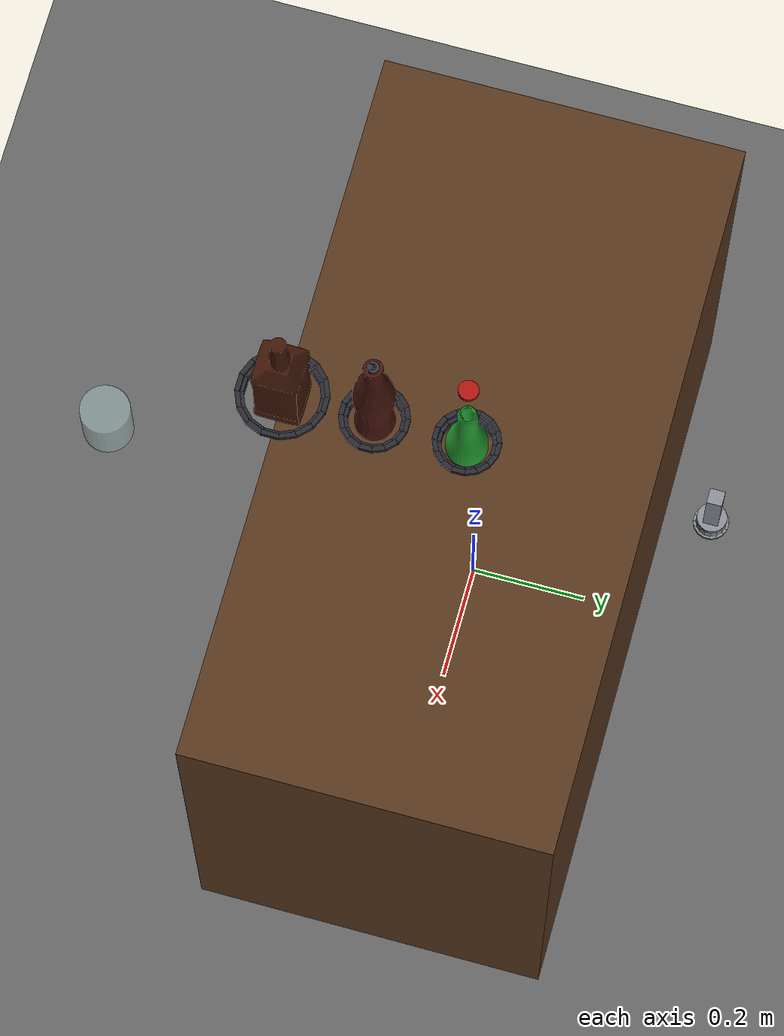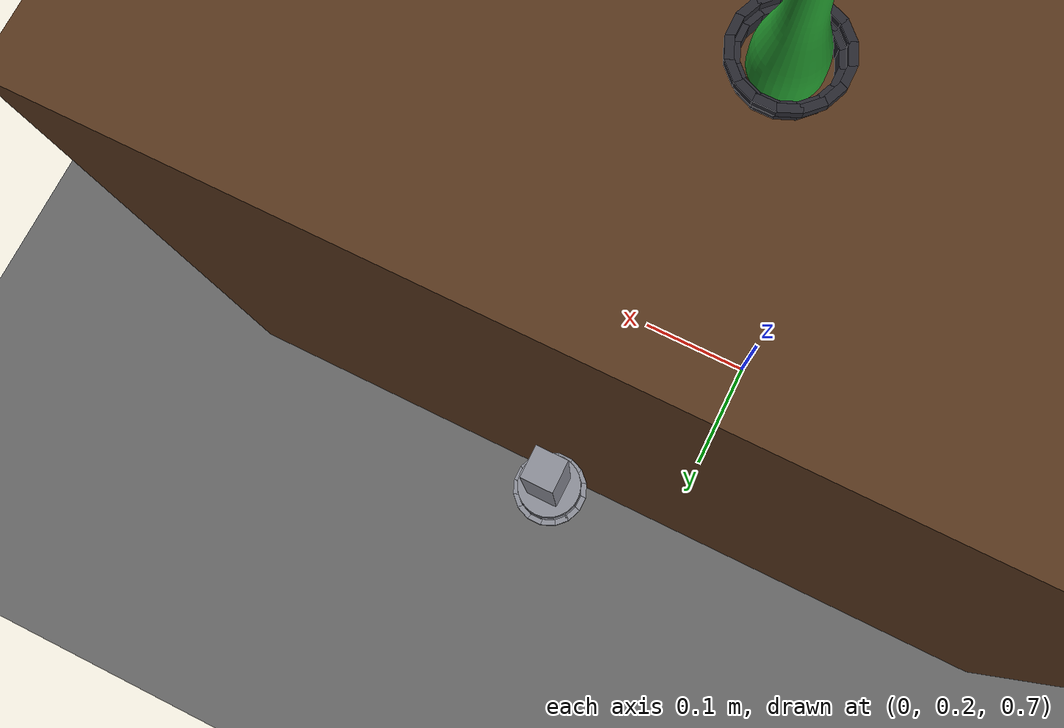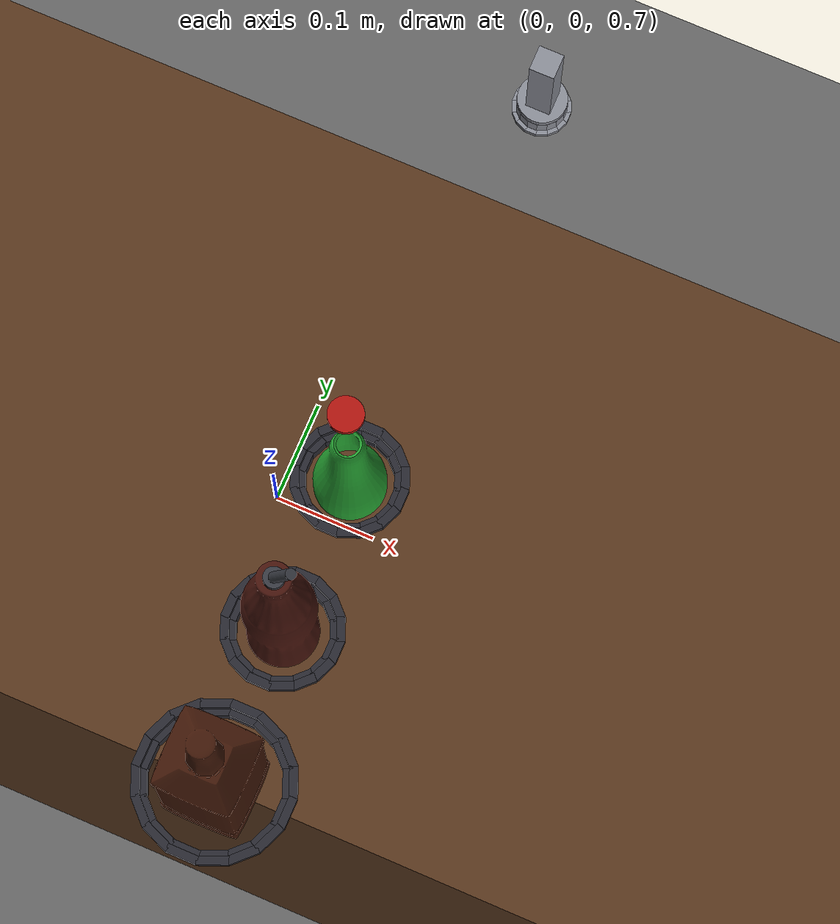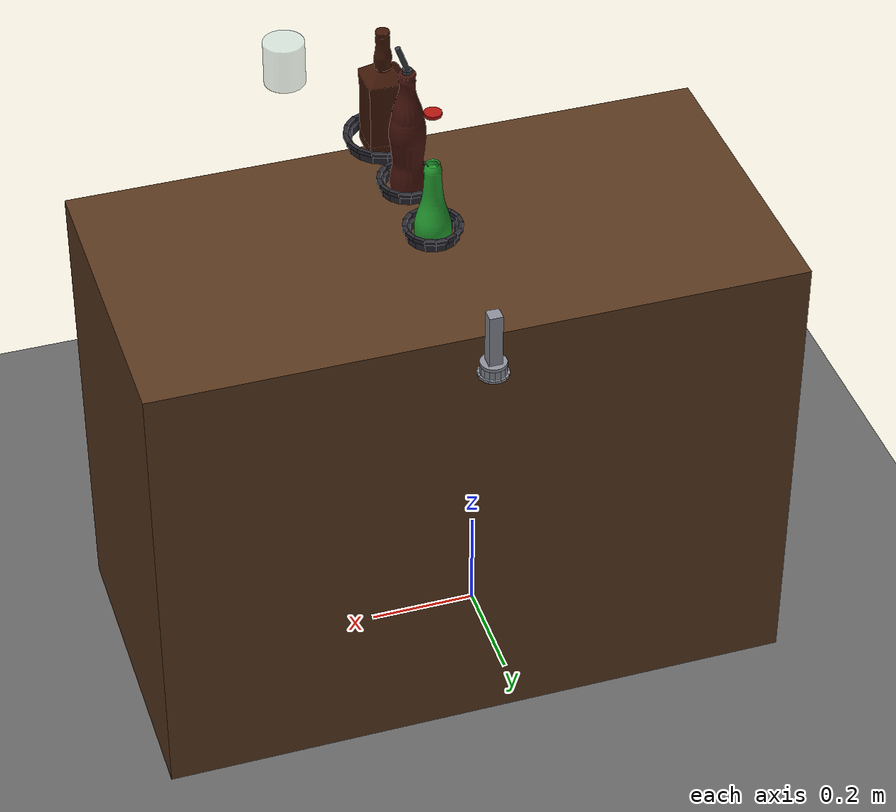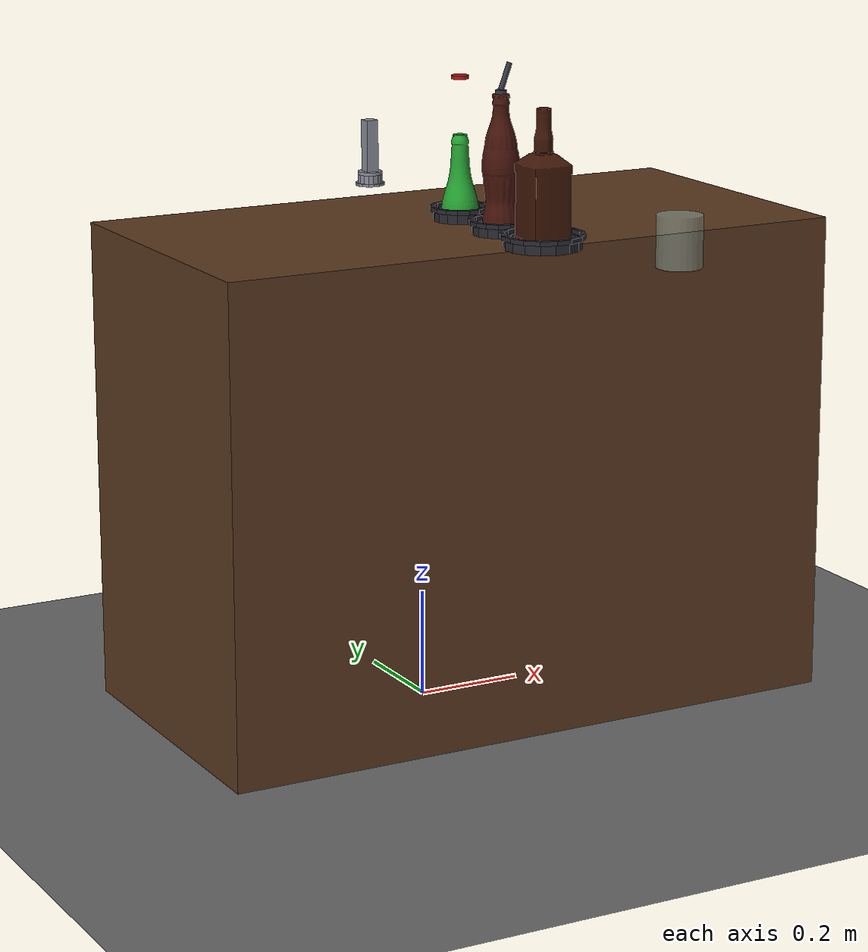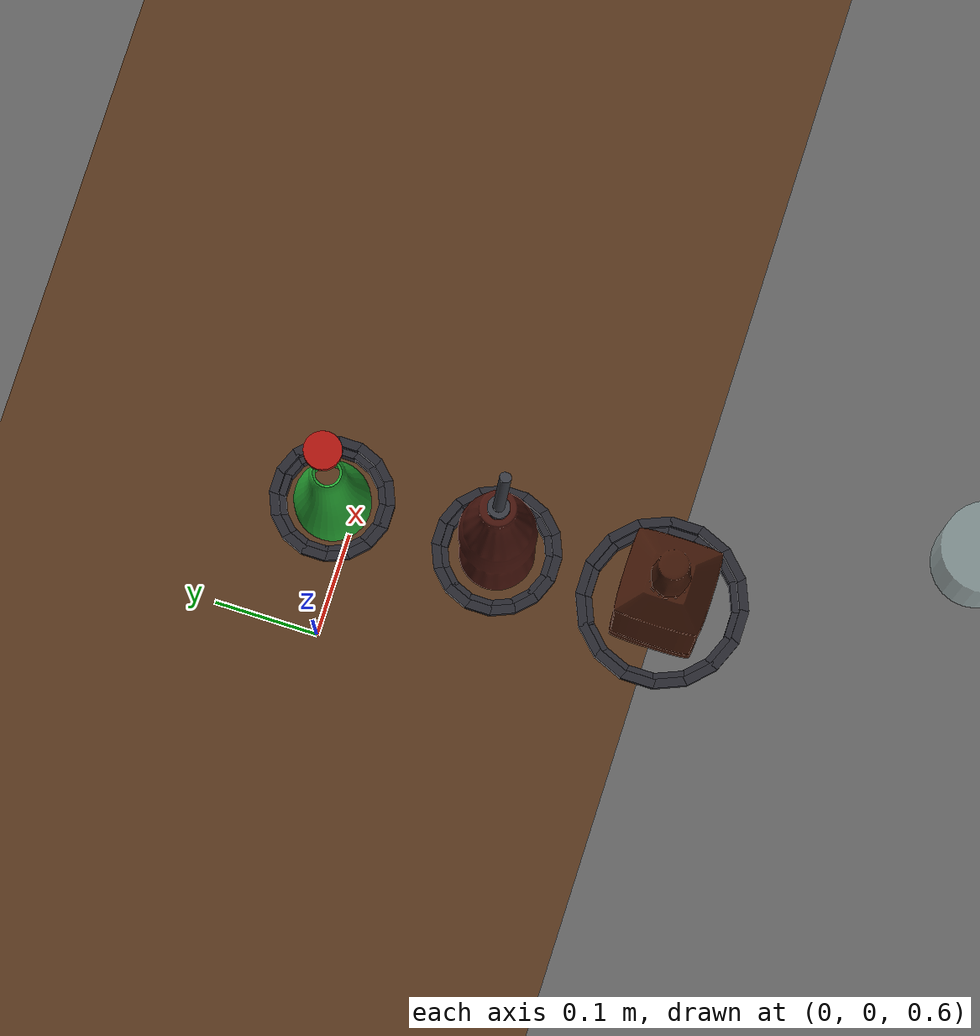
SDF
<?xml version="1.0" ?>
<sdf version="1.9">
  <world name="bar_world">
    <physics name="1ms" type="ignored">
      <max_step_size>0.001</max_step_size>
      <real_time_factor>1.0</real_time_factor>
      <dart>
        <collision_detector>bullet</collision_detector>
      </dart>
    </physics>

    <plugin filename="gz-sim-physics-system" name="gz::sim::systems::Physics"/>
    <plugin filename="gz-sim-user-commands-system" name="gz::sim::systems::UserCommands"/>
    <plugin filename="gz-sim-scene-broadcaster-system" name="gz::sim::systems::SceneBroadcaster"/>
    <plugin filename="gz-sim-sensors-system" name="gz::sim::systems::Sensors">
      <render_engine>ogre2</render_engine>
    </plugin>
    <plugin filename="gz-sim-contact-system" name="gz::sim::systems::Contact"/>

    <light type="directional" name="sun">
      <cast_shadows>true</cast_shadows>
      <pose>0 0 10 0 0 0</pose>
      <diffuse>0.8 0.8 0.8 1</diffuse>
      <specular>0.2 0.2 0.2 1</specular>
      <attenuation>
        <range>1000</range>
        <constant>0.9</constant>
        <linear>0.01</linear>
        <quadratic>0.001</quadratic>
      </attenuation>
      <direction>-0.5 0.1 -0.9</direction>
    </light>

    <model name="ground_plane">
      <static>true</static>
      <link name="link">
        <collision name="collision">
          <geometry>
            <plane>
              <normal>0 0 1</normal>
              <size>100 100</size>
            </plane>
          </geometry>
        </collision>
        <visual name="visual">
          <geometry>
            <plane>
              <normal>0 0 1</normal>
              <size>100 100</size>
            </plane>
          </geometry>
          <material>
            <ambient>0.3 0.3 0.3 1</ambient>
            <diffuse>0.4 0.4 0.4 1</diffuse>
          </material>
        </visual>
      </link>
    </model>

    <include>
      <uri>model://bar_counter</uri>
      <name>bar_counter</name>
      <pose>0.08 0 0.9 0 0 0</pose>
    </include>

    <!-- Label plugins tag objects for the segmentation cameras; the numbers are
         scripts/vlm_labels.py LABEL_IDS (test_vlm_labels.py checks they match). -->
    <include>
      <uri>model://jack_daniels_bottle</uri>
      <name>jack_daniels_bottle</name>
      <plugin filename="gz-sim-label-system" name="gz::sim::systems::Label">
        <label>1</label>
      </plugin>
      <pose>0.08 -0.30 0.9 0 0 0</pose>
    </include>

    <include>
      <uri>model://cola_bottle</uri>
      <name>cola_bottle</name>
      <plugin filename="gz-sim-label-system" name="gz::sim::systems::Label">
        <label>2</label>
      </plugin>
      <pose>0.08 -0.15 0.9 0 0 0</pose>
    </include>

    <include>
      <uri>model://whiskey_stand</uri>
      <name>whiskey_stand</name>
      <pose>0.08 -0.30 0.9 0 0 0</pose>
    </include>

    <include>
      <uri>model://cola_stand</uri>
      <name>cola_stand</name>
      <pose>0.08 -0.15 0.9 0 0 0</pose>
    </include>

    <include>
      <uri>model://beer_stand</uri>
      <name>beer_stand</name>
      <pose>0.08 0.0 0.9 0 0 0</pose>
    </include>

    <include>
      <uri>model://beer_bottle</uri>
      <name>beer_bottle</name>
      <plugin filename="gz-sim-label-system" name="gz::sim::systems::Label">
        <label>3</label>
      </plugin>
      <pose>0.08 0.0 0.9 0 0 0</pose>
    </include>

    <include>
      <uri>model://beer_cap</uri>
      <name>beer_cap</name>
      <pose>0.08 0.0 1.1581 0 0 0</pose>
    </include>

    <!-- ============== each arm's own working station ============== -->

    <include>
      <uri>model://serving_glass</uri>
      <name>serving_glass</name>
      <plugin filename="gz-sim-label-system" name="gz::sim::systems::Label">
        <label>10</label>
      </plugin>
      <pose>0.20 -0.55 0.9 0 0 0</pose>
    </include>

    <include>
      <uri>model://opener_holster</uri>
      <name>opener_holster</name>
      <pose>0.10 0.40 0.9 0 0 0</pose>
    </include>

    <include>
      <uri>model://bottle_opener</uri>
      <name>bottle_opener</name>
      <pose>0.10 0.40 0.9 0 0 0</pose>
    </include>

    <!-- Simulated OAK-D depth on a stand; its pose is restated in bartender_api/config/stand_camera.yaml. -->
    <model name="oak_d_stand">
      <static>true</static>
      <pose>0.75 0 1.35 0 0.493051 3.141593</pose>
      <link name="link">
        <sensor name="stand_depth" type="depth_camera">
          <always_on>true</always_on>
          <update_rate>15</update_rate>
          <topic>/bartender/stand_camera/depth</topic>
          <ignition_frame_id>stand_camera_optical_frame</ignition_frame_id>
          <camera>
            <camera_info_topic>/bartender/stand_camera/camera_info</camera_info_topic>
            <horizontal_fov>1.2566</horizontal_fov>
            <image>
              <width>640</width>
              <height>400</height>
              <format>R_FLOAT32</format>
            </image>
            <clip>
              <near>0.2</near>
              <far>5.0</far>
            </clip>
            <noise>
              <type>gaussian</type>
              <mean>0.0</mean>
              <stddev>0.004</stddev>
            </noise>
          </camera>
        </sensor>
        <!-- Colour twin of stand_depth: same pose, FOV and size, so pixels line up (OAK-D aligns RGB to depth). -->
        <sensor name="stand_rgb" type="camera">
          <always_on>true</always_on>
          <update_rate>15</update_rate>
          <topic>/bartender/stand_camera/rgb</topic>
          <ignition_frame_id>stand_camera_optical_frame</ignition_frame_id>
          <camera>
            <horizontal_fov>1.2566</horizontal_fov>
            <image>
              <width>640</width>
              <height>400</height>
              <format>R8G8B8</format>
            </image>
            <clip>
              <near>0.2</near>
              <far>5.0</far>
            </clip>
          </camera>
        </sensor>
        <sensor name="bartender_stand_camera_segmentation" type="segmentation">
          <always_on>true</always_on>
          <update_rate>15</update_rate>
          <topic>/bartender/stand_camera/segmentation</topic>
          <camera>
            <segmentation_type>semantic</segmentation_type>
            <horizontal_fov>1.2566</horizontal_fov>
            <image>
              <width>640</width>
              <height>400</height>
            </image>
            <clip>
              <near>0.2</near>
              <far>5.0</far>
            </clip>
          </camera>
        </sensor>
      </link>
    </model>

    <model name="overhead_camera">
      <static>true</static>
      <pose>-0.05 -0.30 2.0 0 1.5708 0</pose>
      <link name="link">
        <sensor name="overhead_rgb" type="camera">
          <always_on>true</always_on>
          <update_rate>15</update_rate>
          <topic>/bartender/overhead_camera/image_raw</topic>
          <camera>
            <horizontal_fov>1.2566</horizontal_fov>
            <image>
              <width>320</width>
              <height>240</height>
              <format>R8G8B8</format>
            </image>
            <clip>
              <near>0.2</near>
              <far>3.0</far>
            </clip>
          </camera>
        </sensor>
        <sensor name="bartender_overhead_camera_segmentation" type="segmentation">
          <always_on>true</always_on>
          <update_rate>15</update_rate>
          <topic>/bartender/overhead_camera/segmentation</topic>
          <camera>
            <segmentation_type>semantic</segmentation_type>
            <horizontal_fov>1.2566</horizontal_fov>
            <image>
              <width>320</width>
              <height>240</height>
            </image>
            <clip>
              <near>0.2</near>
              <far>3.0</far>
            </clip>
          </camera>
        </sensor>
      </link>
    </model>

  </world>
</sdf>

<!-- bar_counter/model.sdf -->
<sdf version="1.9">
  <model name="bar_counter">
    <static>true</static>
    <link name="counter_link">
      <visual name="counter_visual">
        <pose>0 0 -0.45 0 0 0</pose>
        <geometry>
          <box>
            <size>1.2 0.6 0.9</size>
          </box>
        </geometry>
        <material>
          <ambient>0.25 0.15 0.08 1</ambient>
          <diffuse>0.35 0.22 0.12 1</diffuse>
          <specular>0.2 0.2 0.2 1</specular>
        </material>
      </visual>

      <collision name="counter_collision">
        <pose>0 0 -0.45 0 0 0</pose>
        <geometry>
          <box>
            <size>1.2 0.6 0.9</size>
          </box>
        </geometry>
        <surface>
          <friction>
            <ode>
              <mu>0.8</mu>
              <mu2>0.8</mu2>
            </ode>
          </friction>
        </surface>
      </collision>
    </link>
  </model>
</sdf>

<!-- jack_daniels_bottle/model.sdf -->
<sdf version="1.9">
  <model name="jack_daniels_bottle">
    <!-- Link origin sits at the center of the bottle's base, so placing the
         model's pose z at table height puts the bottle exactly on the surface. -->
    <link name="bottle_link">
      <inertial>
        <pose>0 0 0.1225 0 0 0</pose>
        <mass>1.0</mass>
        <inertia>
          <ixx>0.005375</ixx>
          <iyy>0.005375</iyy>
          <izz>0.000745</izz>
          <ixy>0</ixy>
          <ixz>0</ixz>
          <iyz>0</iyz>
        </inertia>
      </inertial>

      <visual name="bottle_visual">
        <!-- source mesh is Y-up (Blender OBJ export); rotate +90 deg about X
             so the bottle's height axis becomes Z-up as SDF expects. -->
        <pose>0 0 0 1.570796 0 0</pose>
        <geometry>
          <mesh>
            <uri>meshes/bottle.obj</uri>
          </mesh>
        </geometry>
        <material>
          <ambient>0.05 0.02 0.01 1</ambient>
          <diffuse>0.25 0.09 0.03 1</diffuse>
          <specular>0.4 0.4 0.4 1</specular>
          <emissive>0 0 0 1</emissive>
        </material>
      </visual>

      <!-- Cheap cylinder collision instead of the 34k-face visual mesh, for
           stable, fast grasp physics. -->
      <collision name="bottle_collision">
        <pose>0 0 0.1225 0 0 0</pose>
        <geometry>
          <cylinder>
            <radius>0.0386</radius>
            <length>0.245</length>
          </cylinder>
        </geometry>
        <surface>
          <friction>
            <ode>
              <mu>0.9</mu>
              <mu2>0.9</mu2>
            </ode>
          </friction>
        </surface>
      </collision>
    </link>
  </model>
</sdf>

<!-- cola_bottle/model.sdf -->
<sdf version="1.9">
  <model name="cola_bottle">
    <!-- Link origin sits at the center of the bottle's base, same convention
         as jack_daniels_bottle, so placing the model's pose z at table height
         puts the bottle exactly on the surface. -->
    <link name="cola_link">
      <inertial>
        <pose>0 0 0.11 0 0 0</pose>
        <mass>1.05</mass>
        <inertia>
          <ixx>0.005765</ixx>
          <iyy>0.005765</iyy>
          <izz>0.000593</izz>
          <ixy>0</ixy>
          <ixz>0</ixz>
          <iyz>0</iyz>
        </inertia>
      </inertial>

      <velocity_decay>
        <linear>0.05</linear>
        <angular>0.30</angular>
      </velocity_decay>

      <visual name="cola_visual">
        <pose>0 0 0 1.570796 0 0</pose>
        <geometry>
          <mesh>
            <uri>meshes/cola_bottle.obj</uri>
            <scale>0.065074 0.065074 0.065074</scale>
          </mesh>
        </geometry>
        <material>
          <ambient>0.06 0.02 0.01 1</ambient>
          <diffuse>0.28 0.08 0.05 1</diffuse>
          <specular>0.5 0.5 0.5 1</specular>
          <emissive>0 0 0 1</emissive>
        </material>
      </visual>

      <collision name="cola_base_collision">
        <pose>0 0 0.0200 0 0 0</pose>
        <geometry>
          <cylinder>
            <radius>0.0333</radius>
            <length>0.040</length>
          </cylinder>
        </geometry>
        <surface>
          <friction>
            <ode>
              <mu>0.9</mu>
              <mu2>0.9</mu2>
            </ode>
          </friction>
        </surface>
      </collision>

      <collision name="cola_waist_collision">
        <pose>0 0 0.0600 0 0 0</pose>
        <geometry>
          <cylinder>
            <radius>0.0298</radius>
            <length>0.040</length>
          </cylinder>
        </geometry>
        <surface>
          <friction>
            <ode>
              <mu>0.9</mu>
              <mu2>0.9</mu2>
            </ode>
          </friction>
        </surface>
      </collision>

      <collision name="cola_bulge_collision">
        <pose>0 0 0.1150 0 0 0</pose>
        <geometry>
          <cylinder>
            <radius>0.0336</radius>
            <length>0.070</length>
          </cylinder>
        </geometry>
        <surface>
          <friction>
            <ode>
              <mu>0.9</mu>
              <mu2>0.9</mu2>
            </ode>
          </friction>
        </surface>
      </collision>

      <collision name="cola_shoulder_collision">
        <pose>0 0 0.1725 0 0 0</pose>
        <geometry>
          <cylinder>
            <radius>0.0250</radius>
            <length>0.045</length>
          </cylinder>
        </geometry>
        <surface>
          <friction>
            <ode>
              <mu>0.9</mu>
              <mu2>0.9</mu2>
            </ode>
          </friction>
        </surface>
      </collision>

      <collision name="cola_neck_collision">
        <pose>0 0 0.2225 0 0 0</pose>
        <geometry>
          <cylinder>
            <radius>0.0165</radius>
            <length>0.055</length>
          </cylinder>
        </geometry>
        <surface>
          <friction>
            <ode>
              <mu>0.9</mu>
              <mu2>0.9</mu2>
            </ode>
          </friction>
        </surface>
      </collision>

      <collision name="cola_collar_collision">
        <pose>0 0 0.2410 0 0 0</pose>
        <geometry>
          <cylinder>
            <radius>0.0210</radius>
            <length>0.008</length>
          </cylinder>
        </geometry>
        <surface>
          <friction>
            <ode>
              <mu>0.9</mu>
              <mu2>0.9</mu2>
            </ode>
          </friction>
        </surface>
      </collision>

      <visual name="cola_pourer_body_visual">
        <pose>0 0 0.2460 0 0 0</pose>
        <geometry><cylinder><radius>0.0095</radius><length>0.022</length></cylinder></geometry>
        <material>
          <ambient>0.05 0.05 0.06 1</ambient>
          <diffuse>0.22 0.23 0.26 1</diffuse>
          <specular>0.7 0.7 0.7 1</specular>
        </material>
      </visual>
      <visual name="cola_pourer_spout_visual">
        <pose>0.0086 0 0.2805 0 0.349066 0</pose>
        <geometry><cylinder><radius>0.005</radius><length>0.050</length></cylinder></geometry>
        <material>
          <ambient>0.05 0.05 0.06 1</ambient>
          <diffuse>0.22 0.23 0.26 1</diffuse>
          <specular>0.7 0.7 0.7 1</specular>
        </material>
      </visual>

      <collision name="cola_pourer_body_collision">
        <pose>0 0 0.2460 0 0 0</pose>
        <geometry><cylinder><radius>0.0095</radius><length>0.022</length></cylinder></geometry>
        <surface><friction><ode><mu>0.9</mu><mu2>0.9</mu2></ode></friction></surface>
      </collision>
      <collision name="cola_pourer_spout_collision">
        <pose>0.0086 0 0.2805 0 0.349066 0</pose>
        <geometry><cylinder><radius>0.005</radius><length>0.050</length></cylinder></geometry>
        <surface><friction><ode><mu>0.9</mu><mu2>0.9</mu2></ode></friction></surface>
      </collision>
    </link>
  </model>
</sdf>

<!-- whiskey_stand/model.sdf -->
<!-- GENERATED by ros2_ws/src/bartender_gazebo/scripts/make_bottle_stands.py.
     Edit that script and re-run it; edits here are overwritten. -->
<sdf version="1.9">
  <model name="whiskey_stand">
    <static>true</static>
    <link name="stand_link">
      <visual name="wall_0">
        <pose>0.064000 0.000000 0.009000 0 0 0.000000</pose>
        <geometry><box><size>0.008000 0.027052 0.018000</size></box></geometry>
        <material>
          <ambient>0.10 0.10 0.12 1</ambient>
          <diffuse>0.16 0.16 0.19 1</diffuse>
          <specular>0.05 0.05 0.05 1</specular>
        </material>
      </visual>
      <collision name="wall_collision_0">
        <pose>0.064000 0.000000 0.009000 0 0 0.000000</pose>
        <geometry><box><size>0.008000 0.027052 0.018000</size></box></geometry>
        <surface>
          <friction><ode>
            <mu>1.2</mu>
            <mu2>1.2</mu2>
          </ode></friction>
        </surface>
      </collision>
      <visual name="wall_1">
        <pose>0.059128 0.024492 0.009000 0 0 0.392699</pose>
        <geometry><box><size>0.008000 0.027052 0.018000</size></box></geometry>
        <material>
          <ambient>0.10 0.10 0.12 1</ambient>
          <diffuse>0.16 0.16 0.19 1</diffuse>
          <specular>0.05 0.05 0.05 1</specular>
        </material>
      </visual>
      <collision name="wall_collision_1">
        <pose>0.059128 0.024492 0.009000 0 0 0.392699</pose>
        <geometry><box><size>0.008000 0.027052 0.018000</size></box></geometry>
        <surface>
          <friction><ode>
            <mu>1.2</mu>
            <mu2>1.2</mu2>
          </ode></friction>
        </surface>
      </collision>
      <visual name="wall_2">
        <pose>0.045255 0.045255 0.009000 0 0 0.785398</pose>
        <geometry><box><size>0.008000 0.027052 0.018000</size></box></geometry>
        <material>
          <ambient>0.10 0.10 0.12 1</ambient>
          <diffuse>0.16 0.16 0.19 1</diffuse>
          <specular>0.05 0.05 0.05 1</specular>
        </material>
      </visual>
      <collision name="wall_collision_2">
        <pose>0.045255 0.045255 0.009000 0 0 0.785398</pose>
        <geometry><box><size>0.008000 0.027052 0.018000</size></box></geometry>
        <surface>
          <friction><ode>
            <mu>1.2</mu>
            <mu2>1.2</mu2>
          </ode></friction>
        </surface>
      </collision>
      <visual name="wall_3">
        <pose>0.024492 0.059128 0.009000 0 0 1.178097</pose>
        <geometry><box><size>0.008000 0.027052 0.018000</size></box></geometry>
        <material>
          <ambient>0.10 0.10 0.12 1</ambient>
          <diffuse>0.16 0.16 0.19 1</diffuse>
          <specular>0.05 0.05 0.05 1</specular>
        </material>
      </visual>
      <collision name="wall_collision_3">
        <pose>0.024492 0.059128 0.009000 0 0 1.178097</pose>
        <geometry><box><size>0.008000 0.027052 0.018000</size></box></geometry>
        <surface>
          <friction><ode>
            <mu>1.2</mu>
            <mu2>1.2</mu2>
          </ode></friction>
        </surface>
      </collision>
      <visual name="wall_4">
        <pose>0.000000 0.064000 0.009000 0 0 1.570796</pose>
        <geometry><box><size>0.008000 0.027052 0.018000</size></box></geometry>
        <material>
          <ambient>0.10 0.10 0.12 1</ambient>
          <diffuse>0.16 0.16 0.19 1</diffuse>
          <specular>0.05 0.05 0.05 1</specular>
        </material>
      </visual>
      <collision name="wall_collision_4">
        <pose>0.000000 0.064000 0.009000 0 0 1.570796</pose>
        <geometry><box><size>0.008000 0.027052 0.018000</size></box></geometry>
        <surface>
          <friction><ode>
            <mu>1.2</mu>
            <mu2>1.2</mu2>
          </ode></friction>
        </surface>
      </collision>
      <visual name="wall_5">
        <pose>-0.024492 0.059128 0.009000 0 0 1.963495</pose>
        <geometry><box><size>0.008000 0.027052 0.018000</size></box></geometry>
        <material>
          <ambient>0.10 0.10 0.12 1</ambient>
          <diffuse>0.16 0.16 0.19 1</diffuse>
          <specular>0.05 0.05 0.05 1</specular>
        </material>
      </visual>
      <collision name="wall_collision_5">
        <pose>-0.024492 0.059128 0.009000 0 0 1.963495</pose>
        <geometry><box><size>0.008000 0.027052 0.018000</size></box></geometry>
        <surface>
          <friction><ode>
            <mu>1.2</mu>
            <mu2>1.2</mu2>
          </ode></friction>
        </surface>
      </collision>
      <visual name="wall_6">
        <pose>-0.045255 0.045255 0.009000 0 0 2.356194</pose>
        <geometry><box><size>0.008000 0.027052 0.018000</size></box></geometry>
        <material>
          <ambient>0.10 0.10 0.12 1</ambient>
          <diffuse>0.16 0.16 0.19 1</diffuse>
          <specular>0.05 0.05 0.05 1</specular>
        </material>
      </visual>
      <collision name="wall_collision_6">
        <pose>-0.045255 0.045255 0.009000 0 0 2.356194</pose>
        <geometry><box><size>0.008000 0.027052 0.018000</size></box></geometry>
        <surface>
          <friction><ode>
            <mu>1.2</mu>
            <mu2>1.2</mu2>
          </ode></friction>
        </surface>
      </collision>
      <visual name="wall_7">
        <pose>-0.059128 0.024492 0.009000 0 0 2.748894</pose>
        <geometry><box><size>0.008000 0.027052 0.018000</size></box></geometry>
        <material>
          <ambient>0.10 0.10 0.12 1</ambient>
          <diffuse>0.16 0.16 0.19 1</diffuse>
          <specular>0.05 0.05 0.05 1</specular>
        </material>
      </visual>
      <collision name="wall_collision_7">
        <pose>-0.059128 0.024492 0.009000 0 0 2.748894</pose>
        <geometry><box><size>0.008000 0.027052 0.018000</size></box></geometry>
        <surface>
          <friction><ode>
            <mu>1.2</mu>
            <mu2>1.2</mu2>
          </ode></friction>
        </surface>
      </collision>
      <visual name="wall_8">
        <pose>-0.064000 0.000000 0.009000 0 0 3.141593</pose>
        <geometry><box><size>0.008000 0.027052 0.018000</size></box></geometry>
        <material>
          <ambient>0.10 0.10 0.12 1</ambient>
          <diffuse>0.16 0.16 0.19 1</diffuse>
          <specular>0.05 0.05 0.05 1</specular>
        </material>
      </visual>
      <collision name="wall_collision_8">
        <pose>-0.064000 0.000000 0.009000 0 0 3.141593</pose>
        <geometry><box><size>0.008000 0.027052 0.018000</size></box></geometry>
        <surface>
          <friction><ode>
            <mu>1.2</mu>
            <mu2>1.2</mu2>
          </ode></friction>
        </surface>
      </collision>
      <visual name="wall_9">
        <pose>-0.059128 -0.024492 0.009000 0 0 3.534292</pose>
        <geometry><box><size>0.008000 0.027052 0.018000</size></box></geometry>
        <material>
          <ambient>0.10 0.10 0.12 1</ambient>
          <diffuse>0.16 0.16 0.19 1</diffuse>
          <specular>0.05 0.05 0.05 1</specular>
        </material>
      </visual>
      <collision name="wall_collision_9">
        <pose>-0.059128 -0.024492 0.009000 0 0 3.534292</pose>
        <geometry><box><size>0.008000 0.027052 0.018000</size></box></geometry>
        <surface>
          <friction><ode>
            <mu>1.2</mu>
            <mu2>1.2</mu2>
          </ode></friction>
        </surface>
      </collision>
      <visual name="wall_10">
        <pose>-0.045255 -0.045255 0.009000 0 0 3.926991</pose>
        <geometry><box><size>0.008000 0.027052 0.018000</size></box></geometry>
        <material>
          <ambient>0.10 0.10 0.12 1</ambient>
          <diffuse>0.16 0.16 0.19 1</diffuse>
          <specular>0.05 0.05 0.05 1</specular>
        </material>
      </visual>
      <collision name="wall_collision_10">
        <pose>-0.045255 -0.045255 0.009000 0 0 3.926991</pose>
        <geometry><box><size>0.008000 0.027052 0.018000</size></box></geometry>
        <surface>
          <friction><ode>
            <mu>1.2</mu>
            <mu2>1.2</mu2>
          </ode></friction>
        </surface>
      </collision>
      <visual name="wall_11">
        <pose>-0.024492 -0.059128 0.009000 0 0 4.319690</pose>
        <geometry><box><size>0.008000 0.027052 0.018000</size></box></geometry>
        <material>
          <ambient>0.10 0.10 0.12 1</ambient>
          <diffuse>0.16 0.16 0.19 1</diffuse>
          <specular>0.05 0.05 0.05 1</specular>
        </material>
      </visual>
      <collision name="wall_collision_11">
        <pose>-0.024492 -0.059128 0.009000 0 0 4.319690</pose>
        <geometry><box><size>0.008000 0.027052 0.018000</size></box></geometry>
        <surface>
          <friction><ode>
            <mu>1.2</mu>
            <mu2>1.2</mu2>
          </ode></friction>
        </surface>
      </collision>
      <visual name="wall_12">
        <pose>-0.000000 -0.064000 0.009000 0 0 4.712389</pose>
        <geometry><box><size>0.008000 0.027052 0.018000</size></box></geometry>
        <material>
          <ambient>0.10 0.10 0.12 1</ambient>
          <diffuse>0.16 0.16 0.19 1</diffuse>
          <specular>0.05 0.05 0.05 1</specular>
        </material>
      </visual>
      <collision name="wall_collision_12">
        <pose>-0.000000 -0.064000 0.009000 0 0 4.712389</pose>
        <geometry><box><size>0.008000 0.027052 0.018000</size></box></geometry>
        <surface>
          <friction><ode>
            <mu>1.2</mu>
            <mu2>1.2</mu2>
          </ode></friction>
        </surface>
      </collision>
      <visual name="wall_13">
        <pose>0.024492 -0.059128 0.009000 0 0 5.105088</pose>
        <geometry><box><size>0.008000 0.027052 0.018000</size></box></geometry>
        <material>
          <ambient>0.10 0.10 0.12 1</ambient>
          <diffuse>0.16 0.16 0.19 1</diffuse>
          <specular>0.05 0.05 0.05 1</specular>
        </material>
      </visual>
      <collision name="wall_collision_13">
        <pose>0.024492 -0.059128 0.009000 0 0 5.105088</pose>
        <geometry><box><size>0.008000 0.027052 0.018000</size></box></geometry>
        <surface>
          <friction><ode>
            <mu>1.2</mu>
            <mu2>1.2</mu2>
          </ode></friction>
        </surface>
      </collision>
      <visual name="wall_14">
        <pose>0.045255 -0.045255 0.009000 0 0 5.497787</pose>
        <geometry><box><size>0.008000 0.027052 0.018000</size></box></geometry>
        <material>
          <ambient>0.10 0.10 0.12 1</ambient>
          <diffuse>0.16 0.16 0.19 1</diffuse>
          <specular>0.05 0.05 0.05 1</specular>
        </material>
      </visual>
      <collision name="wall_collision_14">
        <pose>0.045255 -0.045255 0.009000 0 0 5.497787</pose>
        <geometry><box><size>0.008000 0.027052 0.018000</size></box></geometry>
        <surface>
          <friction><ode>
            <mu>1.2</mu>
            <mu2>1.2</mu2>
          </ode></friction>
        </surface>
      </collision>
      <visual name="wall_15">
        <pose>0.059128 -0.024492 0.009000 0 0 5.890486</pose>
        <geometry><box><size>0.008000 0.027052 0.018000</size></box></geometry>
        <material>
          <ambient>0.10 0.10 0.12 1</ambient>
          <diffuse>0.16 0.16 0.19 1</diffuse>
          <specular>0.05 0.05 0.05 1</specular>
        </material>
      </visual>
      <collision name="wall_collision_15">
        <pose>0.059128 -0.024492 0.009000 0 0 5.890486</pose>
        <geometry><box><size>0.008000 0.027052 0.018000</size></box></geometry>
        <surface>
          <friction><ode>
            <mu>1.2</mu>
            <mu2>1.2</mu2>
          </ode></friction>
        </surface>
      </collision>
      <visual name="wall_16">
        <pose>0.070000 0.000000 0.022000 0 0 0.000000</pose>
        <geometry><box><size>0.008000 0.029439 0.008000</size></box></geometry>
        <material>
          <ambient>0.10 0.10 0.12 1</ambient>
          <diffuse>0.16 0.16 0.19 1</diffuse>
          <specular>0.05 0.05 0.05 1</specular>
        </material>
      </visual>
      <collision name="wall_collision_16">
        <pose>0.070000 0.000000 0.022000 0 0 0.000000</pose>
        <geometry><box><size>0.008000 0.029439 0.008000</size></box></geometry>
        <surface>
          <friction><ode>
            <mu>1.2</mu>
            <mu2>1.2</mu2>
          </ode></friction>
        </surface>
      </collision>
      <visual name="wall_17">
        <pose>0.064672 0.026788 0.022000 0 0 0.392699</pose>
        <geometry><box><size>0.008000 0.029439 0.008000</size></box></geometry>
        <material>
          <ambient>0.10 0.10 0.12 1</ambient>
          <diffuse>0.16 0.16 0.19 1</diffuse>
          <specular>0.05 0.05 0.05 1</specular>
        </material>
      </visual>
      <collision name="wall_collision_17">
        <pose>0.064672 0.026788 0.022000 0 0 0.392699</pose>
        <geometry><box><size>0.008000 0.029439 0.008000</size></box></geometry>
        <surface>
          <friction><ode>
            <mu>1.2</mu>
            <mu2>1.2</mu2>
          </ode></friction>
        </surface>
      </collision>
      <visual name="wall_18">
        <pose>0.049497 0.049497 0.022000 0 0 0.785398</pose>
        <geometry><box><size>0.008000 0.029439 0.008000</size></box></geometry>
        <material>
          <ambient>0.10 0.10 0.12 1</ambient>
          <diffuse>0.16 0.16 0.19 1</diffuse>
          <specular>0.05 0.05 0.05 1</specular>
        </material>
      </visual>
      <collision name="wall_collision_18">
        <pose>0.049497 0.049497 0.022000 0 0 0.785398</pose>
        <geometry><box><size>0.008000 0.029439 0.008000</size></box></geometry>
        <surface>
          <friction><ode>
            <mu>1.2</mu>
            <mu2>1.2</mu2>
          </ode></friction>
        </surface>
      </collision>
      <visual name="wall_19">
        <pose>0.026788 0.064672 0.022000 0 0 1.178097</pose>
        <geometry><box><size>0.008000 0.029439 0.008000</size></box></geometry>
        <material>
          <ambient>0.10 0.10 0.12 1</ambient>
          <diffuse>0.16 0.16 0.19 1</diffuse>
          <specular>0.05 0.05 0.05 1</specular>
        </material>
      </visual>
      <collision name="wall_collision_19">
        <pose>0.026788 0.064672 0.022000 0 0 1.178097</pose>
        <geometry><box><size>0.008000 0.029439 0.008000</size></box></geometry>
        <surface>
          <friction><ode>
            <mu>1.2</mu>
            <mu2>1.2</mu2>
          </ode></friction>
        </surface>
      </collision>
      <visual name="wall_20">
        <pose>0.000000 0.070000 0.022000 0 0 1.570796</pose>
        <geometry><box><size>0.008000 0.029439 0.008000</size></box></geometry>
        <material>
          <ambient>0.10 0.10 0.12 1</ambient>
          <diffuse>0.16 0.16 0.19 1</diffuse>
          <specular>0.05 0.05 0.05 1</specular>
        </material>
      </visual>
      <collision name="wall_collision_20">
        <pose>0.000000 0.070000 0.022000 0 0 1.570796</pose>
        <geometry><box><size>0.008000 0.029439 0.008000</size></box></geometry>
        <surface>
          <friction><ode>
            <mu>1.2</mu>
            <mu2>1.2</mu2>
          </ode></friction>
        </surface>
      </collision>
      <visual name="wall_21">
        <pose>-0.026788 0.064672 0.022000 0 0 1.963495</pose>
        <geometry><box><size>0.008000 0.029439 0.008000</size></box></geometry>
        <material>
          <ambient>0.10 0.10 0.12 1</ambient>
          <diffuse>0.16 0.16 0.19 1</diffuse>
          <specular>0.05 0.05 0.05 1</specular>
        </material>
      </visual>
      <collision name="wall_collision_21">
        <pose>-0.026788 0.064672 0.022000 0 0 1.963495</pose>
        <geometry><box><size>0.008000 0.029439 0.008000</size></box></geometry>
        <surface>
          <friction><ode>
            <mu>1.2</mu>
            <mu2>1.2</mu2>
          </ode></friction>
        </surface>
      </collision>
      <visual name="wall_22">
        <pose>-0.049497 0.049497 0.022000 0 0 2.356194</pose>
        <geometry><box><size>0.008000 0.029439 0.008000</size></box></geometry>
        <material>
          <ambient>0.10 0.10 0.12 1</ambient>
          <diffuse>0.16 0.16 0.19 1</diffuse>
          <specular>0.05 0.05 0.05 1</specular>
        </material>
      </visual>
      <collision name="wall_collision_22">
        <pose>-0.049497 0.049497 0.022000 0 0 2.356194</pose>
        <geometry><box><size>0.008000 0.029439 0.008000</size></box></geometry>
        <surface>
          <friction><ode>
            <mu>1.2</mu>
            <mu2>1.2</mu2>
          </ode></friction>
        </surface>
      </collision>
      <visual name="wall_23">
        <pose>-0.064672 0.026788 0.022000 0 0 2.748894</pose>
        <geometry><box><size>0.008000 0.029439 0.008000</size></box></geometry>
        <material>
          <ambient>0.10 0.10 0.12 1</ambient>
          <diffuse>0.16 0.16 0.19 1</diffuse>
          <specular>0.05 0.05 0.05 1</specular>
        </material>
      </visual>
      <collision name="wall_collision_23">
        <pose>-0.064672 0.026788 0.022000 0 0 2.748894</pose>
        <geometry><box><size>0.008000 0.029439 0.008000</size></box></geometry>
        <surface>
          <friction><ode>
            <mu>1.2</mu>
            <mu2>1.2</mu2>
          </ode></friction>
        </surface>
      </collision>
      <visual name="wall_24">
        <pose>-0.070000 0.000000 0.022000 0 0 3.141593</pose>
        <geometry><box><size>0.008000 0.029439 0.008000</size></box></geometry>
        <material>
          <ambient>0.10 0.10 0.12 1</ambient>
          <diffuse>0.16 0.16 0.19 1</diffuse>
          <specular>0.05 0.05 0.05 1</specular>
        </material>
      </visual>
      <collision name="wall_collision_24">
        <pose>-0.070000 0.000000 0.022000 0 0 3.141593</pose>
        <geometry><box><size>0.008000 0.029439 0.008000</size></box></geometry>
        <surface>
          <friction><ode>
            <mu>1.2</mu>
            <mu2>1.2</mu2>
          </ode></friction>
        </surface>
      </collision>
      <visual name="wall_25">
        <pose>-0.064672 -0.026788 0.022000 0 0 3.534292</pose>
        <geometry><box><size>0.008000 0.029439 0.008000</size></box></geometry>
        <material>
          <ambient>0.10 0.10 0.12 1</ambient>
          <diffuse>0.16 0.16 0.19 1</diffuse>
          <specular>0.05 0.05 0.05 1</specular>
        </material>
      </visual>
      <collision name="wall_collision_25">
        <pose>-0.064672 -0.026788 0.022000 0 0 3.534292</pose>
        <geometry><box><size>0.008000 0.029439 0.008000</size></box></geometry>
        <surface>
          <friction><ode>
            <mu>1.2</mu>
            <mu2>1.2</mu2>
          </ode></friction>
        </surface>
      </collision>
      <visual name="wall_26">
        <pose>-0.049497 -0.049497 0.022000 0 0 3.926991</pose>
        <geometry><box><size>0.008000 0.029439 0.008000</size></box></geometry>
        <material>
          <ambient>0.10 0.10 0.12 1</ambient>
          <diffuse>0.16 0.16 0.19 1</diffuse>
          <specular>0.05 0.05 0.05 1</specular>
        </material>
      </visual>
      <collision name="wall_collision_26">
        <pose>-0.049497 -0.049497 0.022000 0 0 3.926991</pose>
        <geometry><box><size>0.008000 0.029439 0.008000</size></box></geometry>
        <surface>
          <friction><ode>
            <mu>1.2</mu>
            <mu2>1.2</mu2>
          </ode></friction>
        </surface>
      </collision>
      <visual name="wall_27">
        <pose>-0.026788 -0.064672 0.022000 0 0 4.319690</pose>
        <geometry><box><size>0.008000 0.029439 0.008000</size></box></geometry>
        <material>
          <ambient>0.10 0.10 0.12 1</ambient>
          <diffuse>0.16 0.16 0.19 1</diffuse>
          <specular>0.05 0.05 0.05 1</specular>
        </material>
      </visual>
      <collision name="wall_collision_27">
        <pose>-0.026788 -0.064672 0.022000 0 0 4.319690</pose>
        <geometry><box><size>0.008000 0.029439 0.008000</size></box></geometry>
        <surface>
          <friction><ode>
            <mu>1.2</mu>
            <mu2>1.2</mu2>
          </ode></friction>
        </surface>
      </collision>
      <visual name="wall_28">
        <pose>-0.000000 -0.070000 0.022000 0 0 4.712389</pose>
        <geometry><box><size>0.008000 0.029439 0.008000</size></box></geometry>
        <material>
          <ambient>0.10 0.10 0.12 1</ambient>
          <diffuse>0.16 0.16 0.19 1</diffuse>
          <specular>0.05 0.05 0.05 1</specular>
        </material>
      </visual>
      <collision name="wall_collision_28">
        <pose>-0.000000 -0.070000 0.022000 0 0 4.712389</pose>
        <geometry><box><size>0.008000 0.029439 0.008000</size></box></geometry>
        <surface>
          <friction><ode>
            <mu>1.2</mu>
            <mu2>1.2</mu2>
          </ode></friction>
        </surface>
      </collision>
      <visual name="wall_29">
        <pose>0.026788 -0.064672 0.022000 0 0 5.105088</pose>
        <geometry><box><size>0.008000 0.029439 0.008000</size></box></geometry>
        <material>
          <ambient>0.10 0.10 0.12 1</ambient>
          <diffuse>0.16 0.16 0.19 1</diffuse>
          <specular>0.05 0.05 0.05 1</specular>
        </material>
      </visual>
      <collision name="wall_collision_29">
        <pose>0.026788 -0.064672 0.022000 0 0 5.105088</pose>
        <geometry><box><size>0.008000 0.029439 0.008000</size></box></geometry>
        <surface>
          <friction><ode>
            <mu>1.2</mu>
            <mu2>1.2</mu2>
          </ode></friction>
        </surface>
      </collision>
      <visual name="wall_30">
        <pose>0.049497 -0.049497 0.022000 0 0 5.497787</pose>
        <geometry><box><size>0.008000 0.029439 0.008000</size></box></geometry>
        <material>
          <ambient>0.10 0.10 0.12 1</ambient>
          <diffuse>0.16 0.16 0.19 1</diffuse>
          <specular>0.05 0.05 0.05 1</specular>
        </material>
      </visual>
      <collision name="wall_collision_30">
        <pose>0.049497 -0.049497 0.022000 0 0 5.497787</pose>
        <geometry><box><size>0.008000 0.029439 0.008000</size></box></geometry>
        <surface>
          <friction><ode>
            <mu>1.2</mu>
            <mu2>1.2</mu2>
          </ode></friction>
        </surface>
      </collision>
      <visual name="wall_31">
        <pose>0.064672 -0.026788 0.022000 0 0 5.890486</pose>
        <geometry><box><size>0.008000 0.029439 0.008000</size></box></geometry>
        <material>
          <ambient>0.10 0.10 0.12 1</ambient>
          <diffuse>0.16 0.16 0.19 1</diffuse>
          <specular>0.05 0.05 0.05 1</specular>
        </material>
      </visual>
      <collision name="wall_collision_31">
        <pose>0.064672 -0.026788 0.022000 0 0 5.890486</pose>
        <geometry><box><size>0.008000 0.029439 0.008000</size></box></geometry>
        <surface>
          <friction><ode>
            <mu>1.2</mu>
            <mu2>1.2</mu2>
          </ode></friction>
        </surface>
      </collision>
    </link>
  </model>
</sdf>

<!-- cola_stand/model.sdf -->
<!-- GENERATED by ros2_ws/src/bartender_gazebo/scripts/make_bottle_stands.py.
     Edit that script and re-run it; edits here are overwritten. -->
<sdf version="1.9">
  <model name="cola_stand">
    <static>true</static>
    <link name="stand_link">
      <visual name="wall_0">
        <pose>0.046000 0.000000 0.009000 0 0 0.000000</pose>
        <geometry><box><size>0.008000 0.019891 0.018000</size></box></geometry>
        <material>
          <ambient>0.10 0.10 0.12 1</ambient>
          <diffuse>0.16 0.16 0.19 1</diffuse>
          <specular>0.05 0.05 0.05 1</specular>
        </material>
      </visual>
      <collision name="wall_collision_0">
        <pose>0.046000 0.000000 0.009000 0 0 0.000000</pose>
        <geometry><box><size>0.008000 0.019891 0.018000</size></box></geometry>
        <surface>
          <friction><ode>
            <mu>1.2</mu>
            <mu2>1.2</mu2>
          </ode></friction>
        </surface>
      </collision>
      <visual name="wall_1">
        <pose>0.042498 0.017603 0.009000 0 0 0.392699</pose>
        <geometry><box><size>0.008000 0.019891 0.018000</size></box></geometry>
        <material>
          <ambient>0.10 0.10 0.12 1</ambient>
          <diffuse>0.16 0.16 0.19 1</diffuse>
          <specular>0.05 0.05 0.05 1</specular>
        </material>
      </visual>
      <collision name="wall_collision_1">
        <pose>0.042498 0.017603 0.009000 0 0 0.392699</pose>
        <geometry><box><size>0.008000 0.019891 0.018000</size></box></geometry>
        <surface>
          <friction><ode>
            <mu>1.2</mu>
            <mu2>1.2</mu2>
          </ode></friction>
        </surface>
      </collision>
      <visual name="wall_2">
        <pose>0.032527 0.032527 0.009000 0 0 0.785398</pose>
        <geometry><box><size>0.008000 0.019891 0.018000</size></box></geometry>
        <material>
          <ambient>0.10 0.10 0.12 1</ambient>
          <diffuse>0.16 0.16 0.19 1</diffuse>
          <specular>0.05 0.05 0.05 1</specular>
        </material>
      </visual>
      <collision name="wall_collision_2">
        <pose>0.032527 0.032527 0.009000 0 0 0.785398</pose>
        <geometry><box><size>0.008000 0.019891 0.018000</size></box></geometry>
        <surface>
          <friction><ode>
            <mu>1.2</mu>
            <mu2>1.2</mu2>
          </ode></friction>
        </surface>
      </collision>
      <visual name="wall_3">
        <pose>0.017603 0.042498 0.009000 0 0 1.178097</pose>
        <geometry><box><size>0.008000 0.019891 0.018000</size></box></geometry>
        <material>
          <ambient>0.10 0.10 0.12 1</ambient>
          <diffuse>0.16 0.16 0.19 1</diffuse>
          <specular>0.05 0.05 0.05 1</specular>
        </material>
      </visual>
      <collision name="wall_collision_3">
        <pose>0.017603 0.042498 0.009000 0 0 1.178097</pose>
        <geometry><box><size>0.008000 0.019891 0.018000</size></box></geometry>
        <surface>
          <friction><ode>
            <mu>1.2</mu>
            <mu2>1.2</mu2>
          </ode></friction>
        </surface>
      </collision>
      <visual name="wall_4">
        <pose>0.000000 0.046000 0.009000 0 0 1.570796</pose>
        <geometry><box><size>0.008000 0.019891 0.018000</size></box></geometry>
        <material>
          <ambient>0.10 0.10 0.12 1</ambient>
          <diffuse>0.16 0.16 0.19 1</diffuse>
          <specular>0.05 0.05 0.05 1</specular>
        </material>
      </visual>
      <collision name="wall_collision_4">
        <pose>0.000000 0.046000 0.009000 0 0 1.570796</pose>
        <geometry><box><size>0.008000 0.019891 0.018000</size></box></geometry>
        <surface>
          <friction><ode>
            <mu>1.2</mu>
            <mu2>1.2</mu2>
          </ode></friction>
        </surface>
      </collision>
      <visual name="wall_5">
        <pose>-0.017603 0.042498 0.009000 0 0 1.963495</pose>
        <geometry><box><size>0.008000 0.019891 0.018000</size></box></geometry>
        <material>
          <ambient>0.10 0.10 0.12 1</ambient>
          <diffuse>0.16 0.16 0.19 1</diffuse>
          <specular>0.05 0.05 0.05 1</specular>
        </material>
      </visual>
      <collision name="wall_collision_5">
        <pose>-0.017603 0.042498 0.009000 0 0 1.963495</pose>
        <geometry><box><size>0.008000 0.019891 0.018000</size></box></geometry>
        <surface>
          <friction><ode>
            <mu>1.2</mu>
            <mu2>1.2</mu2>
          </ode></friction>
        </surface>
      </collision>
      <visual name="wall_6">
        <pose>-0.032527 0.032527 0.009000 0 0 2.356194</pose>
        <geometry><box><size>0.008000 0.019891 0.018000</size></box></geometry>
        <material>
          <ambient>0.10 0.10 0.12 1</ambient>
          <diffuse>0.16 0.16 0.19 1</diffuse>
          <specular>0.05 0.05 0.05 1</specular>
        </material>
      </visual>
      <collision name="wall_collision_6">
        <pose>-0.032527 0.032527 0.009000 0 0 2.356194</pose>
        <geometry><box><size>0.008000 0.019891 0.018000</size></box></geometry>
        <surface>
          <friction><ode>
            <mu>1.2</mu>
            <mu2>1.2</mu2>
          </ode></friction>
        </surface>
      </collision>
      <visual name="wall_7">
        <pose>-0.042498 0.017603 0.009000 0 0 2.748894</pose>
        <geometry><box><size>0.008000 0.019891 0.018000</size></box></geometry>
        <material>
          <ambient>0.10 0.10 0.12 1</ambient>
          <diffuse>0.16 0.16 0.19 1</diffuse>
          <specular>0.05 0.05 0.05 1</specular>
        </material>
      </visual>
      <collision name="wall_collision_7">
        <pose>-0.042498 0.017603 0.009000 0 0 2.748894</pose>
        <geometry><box><size>0.008000 0.019891 0.018000</size></box></geometry>
        <surface>
          <friction><ode>
            <mu>1.2</mu>
            <mu2>1.2</mu2>
          </ode></friction>
        </surface>
      </collision>
      <visual name="wall_8">
        <pose>-0.046000 0.000000 0.009000 0 0 3.141593</pose>
        <geometry><box><size>0.008000 0.019891 0.018000</size></box></geometry>
        <material>
          <ambient>0.10 0.10 0.12 1</ambient>
          <diffuse>0.16 0.16 0.19 1</diffuse>
          <specular>0.05 0.05 0.05 1</specular>
        </material>
      </visual>
      <collision name="wall_collision_8">
        <pose>-0.046000 0.000000 0.009000 0 0 3.141593</pose>
        <geometry><box><size>0.008000 0.019891 0.018000</size></box></geometry>
        <surface>
          <friction><ode>
            <mu>1.2</mu>
            <mu2>1.2</mu2>
          </ode></friction>
        </surface>
      </collision>
      <visual name="wall_9">
        <pose>-0.042498 -0.017603 0.009000 0 0 3.534292</pose>
        <geometry><box><size>0.008000 0.019891 0.018000</size></box></geometry>
        <material>
          <ambient>0.10 0.10 0.12 1</ambient>
          <diffuse>0.16 0.16 0.19 1</diffuse>
          <specular>0.05 0.05 0.05 1</specular>
        </material>
      </visual>
      <collision name="wall_collision_9">
        <pose>-0.042498 -0.017603 0.009000 0 0 3.534292</pose>
        <geometry><box><size>0.008000 0.019891 0.018000</size></box></geometry>
        <surface>
          <friction><ode>
            <mu>1.2</mu>
            <mu2>1.2</mu2>
          </ode></friction>
        </surface>
      </collision>
      <visual name="wall_10">
        <pose>-0.032527 -0.032527 0.009000 0 0 3.926991</pose>
        <geometry><box><size>0.008000 0.019891 0.018000</size></box></geometry>
        <material>
          <ambient>0.10 0.10 0.12 1</ambient>
          <diffuse>0.16 0.16 0.19 1</diffuse>
          <specular>0.05 0.05 0.05 1</specular>
        </material>
      </visual>
      <collision name="wall_collision_10">
        <pose>-0.032527 -0.032527 0.009000 0 0 3.926991</pose>
        <geometry><box><size>0.008000 0.019891 0.018000</size></box></geometry>
        <surface>
          <friction><ode>
            <mu>1.2</mu>
            <mu2>1.2</mu2>
          </ode></friction>
        </surface>
      </collision>
      <visual name="wall_11">
        <pose>-0.017603 -0.042498 0.009000 0 0 4.319690</pose>
        <geometry><box><size>0.008000 0.019891 0.018000</size></box></geometry>
        <material>
          <ambient>0.10 0.10 0.12 1</ambient>
          <diffuse>0.16 0.16 0.19 1</diffuse>
          <specular>0.05 0.05 0.05 1</specular>
        </material>
      </visual>
      <collision name="wall_collision_11">
        <pose>-0.017603 -0.042498 0.009000 0 0 4.319690</pose>
        <geometry><box><size>0.008000 0.019891 0.018000</size></box></geometry>
        <surface>
          <friction><ode>
            <mu>1.2</mu>
            <mu2>1.2</mu2>
          </ode></friction>
        </surface>
      </collision>
      <visual name="wall_12">
        <pose>-0.000000 -0.046000 0.009000 0 0 4.712389</pose>
        <geometry><box><size>0.008000 0.019891 0.018000</size></box></geometry>
        <material>
          <ambient>0.10 0.10 0.12 1</ambient>
          <diffuse>0.16 0.16 0.19 1</diffuse>
          <specular>0.05 0.05 0.05 1</specular>
        </material>
      </visual>
      <collision name="wall_collision_12">
        <pose>-0.000000 -0.046000 0.009000 0 0 4.712389</pose>
        <geometry><box><size>0.008000 0.019891 0.018000</size></box></geometry>
        <surface>
          <friction><ode>
            <mu>1.2</mu>
            <mu2>1.2</mu2>
          </ode></friction>
        </surface>
      </collision>
      <visual name="wall_13">
        <pose>0.017603 -0.042498 0.009000 0 0 5.105088</pose>
        <geometry><box><size>0.008000 0.019891 0.018000</size></box></geometry>
        <material>
          <ambient>0.10 0.10 0.12 1</ambient>
          <diffuse>0.16 0.16 0.19 1</diffuse>
          <specular>0.05 0.05 0.05 1</specular>
        </material>
      </visual>
      <collision name="wall_collision_13">
        <pose>0.017603 -0.042498 0.009000 0 0 5.105088</pose>
        <geometry><box><size>0.008000 0.019891 0.018000</size></box></geometry>
        <surface>
          <friction><ode>
            <mu>1.2</mu>
            <mu2>1.2</mu2>
          </ode></friction>
        </surface>
      </collision>
      <visual name="wall_14">
        <pose>0.032527 -0.032527 0.009000 0 0 5.497787</pose>
        <geometry><box><size>0.008000 0.019891 0.018000</size></box></geometry>
        <material>
          <ambient>0.10 0.10 0.12 1</ambient>
          <diffuse>0.16 0.16 0.19 1</diffuse>
          <specular>0.05 0.05 0.05 1</specular>
        </material>
      </visual>
      <collision name="wall_collision_14">
        <pose>0.032527 -0.032527 0.009000 0 0 5.497787</pose>
        <geometry><box><size>0.008000 0.019891 0.018000</size></box></geometry>
        <surface>
          <friction><ode>
            <mu>1.2</mu>
            <mu2>1.2</mu2>
          </ode></friction>
        </surface>
      </collision>
      <visual name="wall_15">
        <pose>0.042498 -0.017603 0.009000 0 0 5.890486</pose>
        <geometry><box><size>0.008000 0.019891 0.018000</size></box></geometry>
        <material>
          <ambient>0.10 0.10 0.12 1</ambient>
          <diffuse>0.16 0.16 0.19 1</diffuse>
          <specular>0.05 0.05 0.05 1</specular>
        </material>
      </visual>
      <collision name="wall_collision_15">
        <pose>0.042498 -0.017603 0.009000 0 0 5.890486</pose>
        <geometry><box><size>0.008000 0.019891 0.018000</size></box></geometry>
        <surface>
          <friction><ode>
            <mu>1.2</mu>
            <mu2>1.2</mu2>
          </ode></friction>
        </surface>
      </collision>
      <visual name="wall_16">
        <pose>0.052000 0.000000 0.022000 0 0 0.000000</pose>
        <geometry><box><size>0.008000 0.022278 0.008000</size></box></geometry>
        <material>
          <ambient>0.10 0.10 0.12 1</ambient>
          <diffuse>0.16 0.16 0.19 1</diffuse>
          <specular>0.05 0.05 0.05 1</specular>
        </material>
      </visual>
      <collision name="wall_collision_16">
        <pose>0.052000 0.000000 0.022000 0 0 0.000000</pose>
        <geometry><box><size>0.008000 0.022278 0.008000</size></box></geometry>
        <surface>
          <friction><ode>
            <mu>1.2</mu>
            <mu2>1.2</mu2>
          </ode></friction>
        </surface>
      </collision>
      <visual name="wall_17">
        <pose>0.048042 0.019900 0.022000 0 0 0.392699</pose>
        <geometry><box><size>0.008000 0.022278 0.008000</size></box></geometry>
        <material>
          <ambient>0.10 0.10 0.12 1</ambient>
          <diffuse>0.16 0.16 0.19 1</diffuse>
          <specular>0.05 0.05 0.05 1</specular>
        </material>
      </visual>
      <collision name="wall_collision_17">
        <pose>0.048042 0.019900 0.022000 0 0 0.392699</pose>
        <geometry><box><size>0.008000 0.022278 0.008000</size></box></geometry>
        <surface>
          <friction><ode>
            <mu>1.2</mu>
            <mu2>1.2</mu2>
          </ode></friction>
        </surface>
      </collision>
      <visual name="wall_18">
        <pose>0.036770 0.036770 0.022000 0 0 0.785398</pose>
        <geometry><box><size>0.008000 0.022278 0.008000</size></box></geometry>
        <material>
          <ambient>0.10 0.10 0.12 1</ambient>
          <diffuse>0.16 0.16 0.19 1</diffuse>
          <specular>0.05 0.05 0.05 1</specular>
        </material>
      </visual>
      <collision name="wall_collision_18">
        <pose>0.036770 0.036770 0.022000 0 0 0.785398</pose>
        <geometry><box><size>0.008000 0.022278 0.008000</size></box></geometry>
        <surface>
          <friction><ode>
            <mu>1.2</mu>
            <mu2>1.2</mu2>
          </ode></friction>
        </surface>
      </collision>
      <visual name="wall_19">
        <pose>0.019900 0.048042 0.022000 0 0 1.178097</pose>
        <geometry><box><size>0.008000 0.022278 0.008000</size></box></geometry>
        <material>
          <ambient>0.10 0.10 0.12 1</ambient>
          <diffuse>0.16 0.16 0.19 1</diffuse>
          <specular>0.05 0.05 0.05 1</specular>
        </material>
      </visual>
      <collision name="wall_collision_19">
        <pose>0.019900 0.048042 0.022000 0 0 1.178097</pose>
        <geometry><box><size>0.008000 0.022278 0.008000</size></box></geometry>
        <surface>
          <friction><ode>
            <mu>1.2</mu>
            <mu2>1.2</mu2>
          </ode></friction>
        </surface>
      </collision>
      <visual name="wall_20">
        <pose>0.000000 0.052000 0.022000 0 0 1.570796</pose>
        <geometry><box><size>0.008000 0.022278 0.008000</size></box></geometry>
        <material>
          <ambient>0.10 0.10 0.12 1</ambient>
          <diffuse>0.16 0.16 0.19 1</diffuse>
          <specular>0.05 0.05 0.05 1</specular>
        </material>
      </visual>
      <collision name="wall_collision_20">
        <pose>0.000000 0.052000 0.022000 0 0 1.570796</pose>
        <geometry><box><size>0.008000 0.022278 0.008000</size></box></geometry>
        <surface>
          <friction><ode>
            <mu>1.2</mu>
            <mu2>1.2</mu2>
          </ode></friction>
        </surface>
      </collision>
      <visual name="wall_21">
        <pose>-0.019900 0.048042 0.022000 0 0 1.963495</pose>
        <geometry><box><size>0.008000 0.022278 0.008000</size></box></geometry>
        <material>
          <ambient>0.10 0.10 0.12 1</ambient>
          <diffuse>0.16 0.16 0.19 1</diffuse>
          <specular>0.05 0.05 0.05 1</specular>
        </material>
      </visual>
      <collision name="wall_collision_21">
        <pose>-0.019900 0.048042 0.022000 0 0 1.963495</pose>
        <geometry><box><size>0.008000 0.022278 0.008000</size></box></geometry>
        <surface>
          <friction><ode>
            <mu>1.2</mu>
            <mu2>1.2</mu2>
          </ode></friction>
        </surface>
      </collision>
      <visual name="wall_22">
        <pose>-0.036770 0.036770 0.022000 0 0 2.356194</pose>
        <geometry><box><size>0.008000 0.022278 0.008000</size></box></geometry>
        <material>
          <ambient>0.10 0.10 0.12 1</ambient>
          <diffuse>0.16 0.16 0.19 1</diffuse>
          <specular>0.05 0.05 0.05 1</specular>
        </material>
      </visual>
      <collision name="wall_collision_22">
        <pose>-0.036770 0.036770 0.022000 0 0 2.356194</pose>
        <geometry><box><size>0.008000 0.022278 0.008000</size></box></geometry>
        <surface>
          <friction><ode>
            <mu>1.2</mu>
            <mu2>1.2</mu2>
          </ode></friction>
        </surface>
      </collision>
      <visual name="wall_23">
        <pose>-0.048042 0.019900 0.022000 0 0 2.748894</pose>
        <geometry><box><size>0.008000 0.022278 0.008000</size></box></geometry>
        <material>
          <ambient>0.10 0.10 0.12 1</ambient>
          <diffuse>0.16 0.16 0.19 1</diffuse>
          <specular>0.05 0.05 0.05 1</specular>
        </material>
      </visual>
      <collision name="wall_collision_23">
        <pose>-0.048042 0.019900 0.022000 0 0 2.748894</pose>
        <geometry><box><size>0.008000 0.022278 0.008000</size></box></geometry>
        <surface>
          <friction><ode>
            <mu>1.2</mu>
            <mu2>1.2</mu2>
          </ode></friction>
        </surface>
      </collision>
      <visual name="wall_24">
        <pose>-0.052000 0.000000 0.022000 0 0 3.141593</pose>
        <geometry><box><size>0.008000 0.022278 0.008000</size></box></geometry>
        <material>
          <ambient>0.10 0.10 0.12 1</ambient>
          <diffuse>0.16 0.16 0.19 1</diffuse>
          <specular>0.05 0.05 0.05 1</specular>
        </material>
      </visual>
      <collision name="wall_collision_24">
        <pose>-0.052000 0.000000 0.022000 0 0 3.141593</pose>
        <geometry><box><size>0.008000 0.022278 0.008000</size></box></geometry>
        <surface>
          <friction><ode>
            <mu>1.2</mu>
            <mu2>1.2</mu2>
          </ode></friction>
        </surface>
      </collision>
      <visual name="wall_25">
        <pose>-0.048042 -0.019900 0.022000 0 0 3.534292</pose>
        <geometry><box><size>0.008000 0.022278 0.008000</size></box></geometry>
        <material>
          <ambient>0.10 0.10 0.12 1</ambient>
          <diffuse>0.16 0.16 0.19 1</diffuse>
          <specular>0.05 0.05 0.05 1</specular>
        </material>
      </visual>
      <collision name="wall_collision_25">
        <pose>-0.048042 -0.019900 0.022000 0 0 3.534292</pose>
        <geometry><box><size>0.008000 0.022278 0.008000</size></box></geometry>
        <surface>
          <friction><ode>
            <mu>1.2</mu>
            <mu2>1.2</mu2>
          </ode></friction>
        </surface>
      </collision>
      <visual name="wall_26">
        <pose>-0.036770 -0.036770 0.022000 0 0 3.926991</pose>
        <geometry><box><size>0.008000 0.022278 0.008000</size></box></geometry>
        <material>
          <ambient>0.10 0.10 0.12 1</ambient>
          <diffuse>0.16 0.16 0.19 1</diffuse>
          <specular>0.05 0.05 0.05 1</specular>
        </material>
      </visual>
      <collision name="wall_collision_26">
        <pose>-0.036770 -0.036770 0.022000 0 0 3.926991</pose>
        <geometry><box><size>0.008000 0.022278 0.008000</size></box></geometry>
        <surface>
          <friction><ode>
            <mu>1.2</mu>
            <mu2>1.2</mu2>
          </ode></friction>
        </surface>
      </collision>
      <visual name="wall_27">
        <pose>-0.019900 -0.048042 0.022000 0 0 4.319690</pose>
        <geometry><box><size>0.008000 0.022278 0.008000</size></box></geometry>
        <material>
          <ambient>0.10 0.10 0.12 1</ambient>
          <diffuse>0.16 0.16 0.19 1</diffuse>
          <specular>0.05 0.05 0.05 1</specular>
        </material>
      </visual>
      <collision name="wall_collision_27">
        <pose>-0.019900 -0.048042 0.022000 0 0 4.319690</pose>
        <geometry><box><size>0.008000 0.022278 0.008000</size></box></geometry>
        <surface>
          <friction><ode>
            <mu>1.2</mu>
            <mu2>1.2</mu2>
          </ode></friction>
        </surface>
      </collision>
      <visual name="wall_28">
        <pose>-0.000000 -0.052000 0.022000 0 0 4.712389</pose>
        <geometry><box><size>0.008000 0.022278 0.008000</size></box></geometry>
        <material>
          <ambient>0.10 0.10 0.12 1</ambient>
          <diffuse>0.16 0.16 0.19 1</diffuse>
          <specular>0.05 0.05 0.05 1</specular>
        </material>
      </visual>
      <collision name="wall_collision_28">
        <pose>-0.000000 -0.052000 0.022000 0 0 4.712389</pose>
        <geometry><box><size>0.008000 0.022278 0.008000</size></box></geometry>
        <surface>
          <friction><ode>
            <mu>1.2</mu>
            <mu2>1.2</mu2>
          </ode></friction>
        </surface>
      </collision>
      <visual name="wall_29">
        <pose>0.019900 -0.048042 0.022000 0 0 5.105088</pose>
        <geometry><box><size>0.008000 0.022278 0.008000</size></box></geometry>
        <material>
          <ambient>0.10 0.10 0.12 1</ambient>
          <diffuse>0.16 0.16 0.19 1</diffuse>
          <specular>0.05 0.05 0.05 1</specular>
        </material>
      </visual>
      <collision name="wall_collision_29">
        <pose>0.019900 -0.048042 0.022000 0 0 5.105088</pose>
        <geometry><box><size>0.008000 0.022278 0.008000</size></box></geometry>
        <surface>
          <friction><ode>
            <mu>1.2</mu>
            <mu2>1.2</mu2>
          </ode></friction>
        </surface>
      </collision>
      <visual name="wall_30">
        <pose>0.036770 -0.036770 0.022000 0 0 5.497787</pose>
        <geometry><box><size>0.008000 0.022278 0.008000</size></box></geometry>
        <material>
          <ambient>0.10 0.10 0.12 1</ambient>
          <diffuse>0.16 0.16 0.19 1</diffuse>
          <specular>0.05 0.05 0.05 1</specular>
        </material>
      </visual>
      <collision name="wall_collision_30">
        <pose>0.036770 -0.036770 0.022000 0 0 5.497787</pose>
        <geometry><box><size>0.008000 0.022278 0.008000</size></box></geometry>
        <surface>
          <friction><ode>
            <mu>1.2</mu>
            <mu2>1.2</mu2>
          </ode></friction>
        </surface>
      </collision>
      <visual name="wall_31">
        <pose>0.048042 -0.019900 0.022000 0 0 5.890486</pose>
        <geometry><box><size>0.008000 0.022278 0.008000</size></box></geometry>
        <material>
          <ambient>0.10 0.10 0.12 1</ambient>
          <diffuse>0.16 0.16 0.19 1</diffuse>
          <specular>0.05 0.05 0.05 1</specular>
        </material>
      </visual>
      <collision name="wall_collision_31">
        <pose>0.048042 -0.019900 0.022000 0 0 5.890486</pose>
        <geometry><box><size>0.008000 0.022278 0.008000</size></box></geometry>
        <surface>
          <friction><ode>
            <mu>1.2</mu>
            <mu2>1.2</mu2>
          </ode></friction>
        </surface>
      </collision>
    </link>
  </model>
</sdf>

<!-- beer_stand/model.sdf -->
<!-- GENERATED by ros2_ws/src/bartender_gazebo/scripts/make_bottle_stands.py.
     Edit that script and re-run it; edits here are overwritten. -->
<sdf version="1.9">
  <model name="beer_stand">
    <static>true</static>
    <link name="stand_link">
      <visual name="wall_0">
        <pose>0.044000 0.000000 0.009000 0 0 0.000000</pose>
        <geometry><box><size>0.008000 0.019096 0.018000</size></box></geometry>
        <material>
          <ambient>0.10 0.10 0.12 1</ambient>
          <diffuse>0.16 0.16 0.19 1</diffuse>
          <specular>0.05 0.05 0.05 1</specular>
        </material>
      </visual>
      <collision name="wall_collision_0">
        <pose>0.044000 0.000000 0.009000 0 0 0.000000</pose>
        <geometry><box><size>0.008000 0.019096 0.018000</size></box></geometry>
        <surface>
          <friction><ode>
            <mu>1.2</mu>
            <mu2>1.2</mu2>
          </ode></friction>
        </surface>
      </collision>
      <visual name="wall_1">
        <pose>0.040651 0.016838 0.009000 0 0 0.392699</pose>
        <geometry><box><size>0.008000 0.019096 0.018000</size></box></geometry>
        <material>
          <ambient>0.10 0.10 0.12 1</ambient>
          <diffuse>0.16 0.16 0.19 1</diffuse>
          <specular>0.05 0.05 0.05 1</specular>
        </material>
      </visual>
      <collision name="wall_collision_1">
        <pose>0.040651 0.016838 0.009000 0 0 0.392699</pose>
        <geometry><box><size>0.008000 0.019096 0.018000</size></box></geometry>
        <surface>
          <friction><ode>
            <mu>1.2</mu>
            <mu2>1.2</mu2>
          </ode></friction>
        </surface>
      </collision>
      <visual name="wall_2">
        <pose>0.031113 0.031113 0.009000 0 0 0.785398</pose>
        <geometry><box><size>0.008000 0.019096 0.018000</size></box></geometry>
        <material>
          <ambient>0.10 0.10 0.12 1</ambient>
          <diffuse>0.16 0.16 0.19 1</diffuse>
          <specular>0.05 0.05 0.05 1</specular>
        </material>
      </visual>
      <collision name="wall_collision_2">
        <pose>0.031113 0.031113 0.009000 0 0 0.785398</pose>
        <geometry><box><size>0.008000 0.019096 0.018000</size></box></geometry>
        <surface>
          <friction><ode>
            <mu>1.2</mu>
            <mu2>1.2</mu2>
          </ode></friction>
        </surface>
      </collision>
      <visual name="wall_3">
        <pose>0.016838 0.040651 0.009000 0 0 1.178097</pose>
        <geometry><box><size>0.008000 0.019096 0.018000</size></box></geometry>
        <material>
          <ambient>0.10 0.10 0.12 1</ambient>
          <diffuse>0.16 0.16 0.19 1</diffuse>
          <specular>0.05 0.05 0.05 1</specular>
        </material>
      </visual>
      <collision name="wall_collision_3">
        <pose>0.016838 0.040651 0.009000 0 0 1.178097</pose>
        <geometry><box><size>0.008000 0.019096 0.018000</size></box></geometry>
        <surface>
          <friction><ode>
            <mu>1.2</mu>
            <mu2>1.2</mu2>
          </ode></friction>
        </surface>
      </collision>
      <visual name="wall_4">
        <pose>0.000000 0.044000 0.009000 0 0 1.570796</pose>
        <geometry><box><size>0.008000 0.019096 0.018000</size></box></geometry>
        <material>
          <ambient>0.10 0.10 0.12 1</ambient>
          <diffuse>0.16 0.16 0.19 1</diffuse>
          <specular>0.05 0.05 0.05 1</specular>
        </material>
      </visual>
      <collision name="wall_collision_4">
        <pose>0.000000 0.044000 0.009000 0 0 1.570796</pose>
        <geometry><box><size>0.008000 0.019096 0.018000</size></box></geometry>
        <surface>
          <friction><ode>
            <mu>1.2</mu>
            <mu2>1.2</mu2>
          </ode></friction>
        </surface>
      </collision>
      <visual name="wall_5">
        <pose>-0.016838 0.040651 0.009000 0 0 1.963495</pose>
        <geometry><box><size>0.008000 0.019096 0.018000</size></box></geometry>
        <material>
          <ambient>0.10 0.10 0.12 1</ambient>
          <diffuse>0.16 0.16 0.19 1</diffuse>
          <specular>0.05 0.05 0.05 1</specular>
        </material>
      </visual>
      <collision name="wall_collision_5">
        <pose>-0.016838 0.040651 0.009000 0 0 1.963495</pose>
        <geometry><box><size>0.008000 0.019096 0.018000</size></box></geometry>
        <surface>
          <friction><ode>
            <mu>1.2</mu>
            <mu2>1.2</mu2>
          </ode></friction>
        </surface>
      </collision>
      <visual name="wall_6">
        <pose>-0.031113 0.031113 0.009000 0 0 2.356194</pose>
        <geometry><box><size>0.008000 0.019096 0.018000</size></box></geometry>
        <material>
          <ambient>0.10 0.10 0.12 1</ambient>
          <diffuse>0.16 0.16 0.19 1</diffuse>
          <specular>0.05 0.05 0.05 1</specular>
        </material>
      </visual>
      <collision name="wall_collision_6">
        <pose>-0.031113 0.031113 0.009000 0 0 2.356194</pose>
        <geometry><box><size>0.008000 0.019096 0.018000</size></box></geometry>
        <surface>
          <friction><ode>
            <mu>1.2</mu>
            <mu2>1.2</mu2>
          </ode></friction>
        </surface>
      </collision>
      <visual name="wall_7">
        <pose>-0.040651 0.016838 0.009000 0 0 2.748894</pose>
        <geometry><box><size>0.008000 0.019096 0.018000</size></box></geometry>
        <material>
          <ambient>0.10 0.10 0.12 1</ambient>
          <diffuse>0.16 0.16 0.19 1</diffuse>
          <specular>0.05 0.05 0.05 1</specular>
        </material>
      </visual>
      <collision name="wall_collision_7">
        <pose>-0.040651 0.016838 0.009000 0 0 2.748894</pose>
        <geometry><box><size>0.008000 0.019096 0.018000</size></box></geometry>
        <surface>
          <friction><ode>
            <mu>1.2</mu>
            <mu2>1.2</mu2>
          </ode></friction>
        </surface>
      </collision>
      <visual name="wall_8">
        <pose>-0.044000 0.000000 0.009000 0 0 3.141593</pose>
        <geometry><box><size>0.008000 0.019096 0.018000</size></box></geometry>
        <material>
          <ambient>0.10 0.10 0.12 1</ambient>
          <diffuse>0.16 0.16 0.19 1</diffuse>
          <specular>0.05 0.05 0.05 1</specular>
        </material>
      </visual>
      <collision name="wall_collision_8">
        <pose>-0.044000 0.000000 0.009000 0 0 3.141593</pose>
        <geometry><box><size>0.008000 0.019096 0.018000</size></box></geometry>
        <surface>
          <friction><ode>
            <mu>1.2</mu>
            <mu2>1.2</mu2>
          </ode></friction>
        </surface>
      </collision>
      <visual name="wall_9">
        <pose>-0.040651 -0.016838 0.009000 0 0 3.534292</pose>
        <geometry><box><size>0.008000 0.019096 0.018000</size></box></geometry>
        <material>
          <ambient>0.10 0.10 0.12 1</ambient>
          <diffuse>0.16 0.16 0.19 1</diffuse>
          <specular>0.05 0.05 0.05 1</specular>
        </material>
      </visual>
      <collision name="wall_collision_9">
        <pose>-0.040651 -0.016838 0.009000 0 0 3.534292</pose>
        <geometry><box><size>0.008000 0.019096 0.018000</size></box></geometry>
        <surface>
          <friction><ode>
            <mu>1.2</mu>
            <mu2>1.2</mu2>
          </ode></friction>
        </surface>
      </collision>
      <visual name="wall_10">
        <pose>-0.031113 -0.031113 0.009000 0 0 3.926991</pose>
        <geometry><box><size>0.008000 0.019096 0.018000</size></box></geometry>
        <material>
          <ambient>0.10 0.10 0.12 1</ambient>
          <diffuse>0.16 0.16 0.19 1</diffuse>
          <specular>0.05 0.05 0.05 1</specular>
        </material>
      </visual>
      <collision name="wall_collision_10">
        <pose>-0.031113 -0.031113 0.009000 0 0 3.926991</pose>
        <geometry><box><size>0.008000 0.019096 0.018000</size></box></geometry>
        <surface>
          <friction><ode>
            <mu>1.2</mu>
            <mu2>1.2</mu2>
          </ode></friction>
        </surface>
      </collision>
      <visual name="wall_11">
        <pose>-0.016838 -0.040651 0.009000 0 0 4.319690</pose>
        <geometry><box><size>0.008000 0.019096 0.018000</size></box></geometry>
        <material>
          <ambient>0.10 0.10 0.12 1</ambient>
          <diffuse>0.16 0.16 0.19 1</diffuse>
          <specular>0.05 0.05 0.05 1</specular>
        </material>
      </visual>
      <collision name="wall_collision_11">
        <pose>-0.016838 -0.040651 0.009000 0 0 4.319690</pose>
        <geometry><box><size>0.008000 0.019096 0.018000</size></box></geometry>
        <surface>
          <friction><ode>
            <mu>1.2</mu>
            <mu2>1.2</mu2>
          </ode></friction>
        </surface>
      </collision>
      <visual name="wall_12">
        <pose>-0.000000 -0.044000 0.009000 0 0 4.712389</pose>
        <geometry><box><size>0.008000 0.019096 0.018000</size></box></geometry>
        <material>
          <ambient>0.10 0.10 0.12 1</ambient>
          <diffuse>0.16 0.16 0.19 1</diffuse>
          <specular>0.05 0.05 0.05 1</specular>
        </material>
      </visual>
      <collision name="wall_collision_12">
        <pose>-0.000000 -0.044000 0.009000 0 0 4.712389</pose>
        <geometry><box><size>0.008000 0.019096 0.018000</size></box></geometry>
        <surface>
          <friction><ode>
            <mu>1.2</mu>
            <mu2>1.2</mu2>
          </ode></friction>
        </surface>
      </collision>
      <visual name="wall_13">
        <pose>0.016838 -0.040651 0.009000 0 0 5.105088</pose>
        <geometry><box><size>0.008000 0.019096 0.018000</size></box></geometry>
        <material>
          <ambient>0.10 0.10 0.12 1</ambient>
          <diffuse>0.16 0.16 0.19 1</diffuse>
          <specular>0.05 0.05 0.05 1</specular>
        </material>
      </visual>
      <collision name="wall_collision_13">
        <pose>0.016838 -0.040651 0.009000 0 0 5.105088</pose>
        <geometry><box><size>0.008000 0.019096 0.018000</size></box></geometry>
        <surface>
          <friction><ode>
            <mu>1.2</mu>
            <mu2>1.2</mu2>
          </ode></friction>
        </surface>
      </collision>
      <visual name="wall_14">
        <pose>0.031113 -0.031113 0.009000 0 0 5.497787</pose>
        <geometry><box><size>0.008000 0.019096 0.018000</size></box></geometry>
        <material>
          <ambient>0.10 0.10 0.12 1</ambient>
          <diffuse>0.16 0.16 0.19 1</diffuse>
          <specular>0.05 0.05 0.05 1</specular>
        </material>
      </visual>
      <collision name="wall_collision_14">
        <pose>0.031113 -0.031113 0.009000 0 0 5.497787</pose>
        <geometry><box><size>0.008000 0.019096 0.018000</size></box></geometry>
        <surface>
          <friction><ode>
            <mu>1.2</mu>
            <mu2>1.2</mu2>
          </ode></friction>
        </surface>
      </collision>
      <visual name="wall_15">
        <pose>0.040651 -0.016838 0.009000 0 0 5.890486</pose>
        <geometry><box><size>0.008000 0.019096 0.018000</size></box></geometry>
        <material>
          <ambient>0.10 0.10 0.12 1</ambient>
          <diffuse>0.16 0.16 0.19 1</diffuse>
          <specular>0.05 0.05 0.05 1</specular>
        </material>
      </visual>
      <collision name="wall_collision_15">
        <pose>0.040651 -0.016838 0.009000 0 0 5.890486</pose>
        <geometry><box><size>0.008000 0.019096 0.018000</size></box></geometry>
        <surface>
          <friction><ode>
            <mu>1.2</mu>
            <mu2>1.2</mu2>
          </ode></friction>
        </surface>
      </collision>
      <visual name="wall_16">
        <pose>0.050000 0.000000 0.022000 0 0 0.000000</pose>
        <geometry><box><size>0.008000 0.021483 0.008000</size></box></geometry>
        <material>
          <ambient>0.10 0.10 0.12 1</ambient>
          <diffuse>0.16 0.16 0.19 1</diffuse>
          <specular>0.05 0.05 0.05 1</specular>
        </material>
      </visual>
      <collision name="wall_collision_16">
        <pose>0.050000 0.000000 0.022000 0 0 0.000000</pose>
        <geometry><box><size>0.008000 0.021483 0.008000</size></box></geometry>
        <surface>
          <friction><ode>
            <mu>1.2</mu>
            <mu2>1.2</mu2>
          </ode></friction>
        </surface>
      </collision>
      <visual name="wall_17">
        <pose>0.046194 0.019134 0.022000 0 0 0.392699</pose>
        <geometry><box><size>0.008000 0.021483 0.008000</size></box></geometry>
        <material>
          <ambient>0.10 0.10 0.12 1</ambient>
          <diffuse>0.16 0.16 0.19 1</diffuse>
          <specular>0.05 0.05 0.05 1</specular>
        </material>
      </visual>
      <collision name="wall_collision_17">
        <pose>0.046194 0.019134 0.022000 0 0 0.392699</pose>
        <geometry><box><size>0.008000 0.021483 0.008000</size></box></geometry>
        <surface>
          <friction><ode>
            <mu>1.2</mu>
            <mu2>1.2</mu2>
          </ode></friction>
        </surface>
      </collision>
      <visual name="wall_18">
        <pose>0.035355 0.035355 0.022000 0 0 0.785398</pose>
        <geometry><box><size>0.008000 0.021483 0.008000</size></box></geometry>
        <material>
          <ambient>0.10 0.10 0.12 1</ambient>
          <diffuse>0.16 0.16 0.19 1</diffuse>
          <specular>0.05 0.05 0.05 1</specular>
        </material>
      </visual>
      <collision name="wall_collision_18">
        <pose>0.035355 0.035355 0.022000 0 0 0.785398</pose>
        <geometry><box><size>0.008000 0.021483 0.008000</size></box></geometry>
        <surface>
          <friction><ode>
            <mu>1.2</mu>
            <mu2>1.2</mu2>
          </ode></friction>
        </surface>
      </collision>
      <visual name="wall_19">
        <pose>0.019134 0.046194 0.022000 0 0 1.178097</pose>
        <geometry><box><size>0.008000 0.021483 0.008000</size></box></geometry>
        <material>
          <ambient>0.10 0.10 0.12 1</ambient>
          <diffuse>0.16 0.16 0.19 1</diffuse>
          <specular>0.05 0.05 0.05 1</specular>
        </material>
      </visual>
      <collision name="wall_collision_19">
        <pose>0.019134 0.046194 0.022000 0 0 1.178097</pose>
        <geometry><box><size>0.008000 0.021483 0.008000</size></box></geometry>
        <surface>
          <friction><ode>
            <mu>1.2</mu>
            <mu2>1.2</mu2>
          </ode></friction>
        </surface>
      </collision>
      <visual name="wall_20">
        <pose>0.000000 0.050000 0.022000 0 0 1.570796</pose>
        <geometry><box><size>0.008000 0.021483 0.008000</size></box></geometry>
        <material>
          <ambient>0.10 0.10 0.12 1</ambient>
          <diffuse>0.16 0.16 0.19 1</diffuse>
          <specular>0.05 0.05 0.05 1</specular>
        </material>
      </visual>
      <collision name="wall_collision_20">
        <pose>0.000000 0.050000 0.022000 0 0 1.570796</pose>
        <geometry><box><size>0.008000 0.021483 0.008000</size></box></geometry>
        <surface>
          <friction><ode>
            <mu>1.2</mu>
            <mu2>1.2</mu2>
          </ode></friction>
        </surface>
      </collision>
      <visual name="wall_21">
        <pose>-0.019134 0.046194 0.022000 0 0 1.963495</pose>
        <geometry><box><size>0.008000 0.021483 0.008000</size></box></geometry>
        <material>
          <ambient>0.10 0.10 0.12 1</ambient>
          <diffuse>0.16 0.16 0.19 1</diffuse>
          <specular>0.05 0.05 0.05 1</specular>
        </material>
      </visual>
      <collision name="wall_collision_21">
        <pose>-0.019134 0.046194 0.022000 0 0 1.963495</pose>
        <geometry><box><size>0.008000 0.021483 0.008000</size></box></geometry>
        <surface>
          <friction><ode>
            <mu>1.2</mu>
            <mu2>1.2</mu2>
          </ode></friction>
        </surface>
      </collision>
      <visual name="wall_22">
        <pose>-0.035355 0.035355 0.022000 0 0 2.356194</pose>
        <geometry><box><size>0.008000 0.021483 0.008000</size></box></geometry>
        <material>
          <ambient>0.10 0.10 0.12 1</ambient>
          <diffuse>0.16 0.16 0.19 1</diffuse>
          <specular>0.05 0.05 0.05 1</specular>
        </material>
      </visual>
      <collision name="wall_collision_22">
        <pose>-0.035355 0.035355 0.022000 0 0 2.356194</pose>
        <geometry><box><size>0.008000 0.021483 0.008000</size></box></geometry>
        <surface>
          <friction><ode>
            <mu>1.2</mu>
            <mu2>1.2</mu2>
          </ode></friction>
        </surface>
      </collision>
      <visual name="wall_23">
        <pose>-0.046194 0.019134 0.022000 0 0 2.748894</pose>
        <geometry><box><size>0.008000 0.021483 0.008000</size></box></geometry>
        <material>
          <ambient>0.10 0.10 0.12 1</ambient>
          <diffuse>0.16 0.16 0.19 1</diffuse>
          <specular>0.05 0.05 0.05 1</specular>
        </material>
      </visual>
      <collision name="wall_collision_23">
        <pose>-0.046194 0.019134 0.022000 0 0 2.748894</pose>
        <geometry><box><size>0.008000 0.021483 0.008000</size></box></geometry>
        <surface>
          <friction><ode>
            <mu>1.2</mu>
            <mu2>1.2</mu2>
          </ode></friction>
        </surface>
      </collision>
      <visual name="wall_24">
        <pose>-0.050000 0.000000 0.022000 0 0 3.141593</pose>
        <geometry><box><size>0.008000 0.021483 0.008000</size></box></geometry>
        <material>
          <ambient>0.10 0.10 0.12 1</ambient>
          <diffuse>0.16 0.16 0.19 1</diffuse>
          <specular>0.05 0.05 0.05 1</specular>
        </material>
      </visual>
      <collision name="wall_collision_24">
        <pose>-0.050000 0.000000 0.022000 0 0 3.141593</pose>
        <geometry><box><size>0.008000 0.021483 0.008000</size></box></geometry>
        <surface>
          <friction><ode>
            <mu>1.2</mu>
            <mu2>1.2</mu2>
          </ode></friction>
        </surface>
      </collision>
      <visual name="wall_25">
        <pose>-0.046194 -0.019134 0.022000 0 0 3.534292</pose>
        <geometry><box><size>0.008000 0.021483 0.008000</size></box></geometry>
        <material>
          <ambient>0.10 0.10 0.12 1</ambient>
          <diffuse>0.16 0.16 0.19 1</diffuse>
          <specular>0.05 0.05 0.05 1</specular>
        </material>
      </visual>
      <collision name="wall_collision_25">
        <pose>-0.046194 -0.019134 0.022000 0 0 3.534292</pose>
        <geometry><box><size>0.008000 0.021483 0.008000</size></box></geometry>
        <surface>
          <friction><ode>
            <mu>1.2</mu>
            <mu2>1.2</mu2>
          </ode></friction>
        </surface>
      </collision>
      <visual name="wall_26">
        <pose>-0.035355 -0.035355 0.022000 0 0 3.926991</pose>
        <geometry><box><size>0.008000 0.021483 0.008000</size></box></geometry>
        <material>
          <ambient>0.10 0.10 0.12 1</ambient>
          <diffuse>0.16 0.16 0.19 1</diffuse>
          <specular>0.05 0.05 0.05 1</specular>
        </material>
      </visual>
      <collision name="wall_collision_26">
        <pose>-0.035355 -0.035355 0.022000 0 0 3.926991</pose>
        <geometry><box><size>0.008000 0.021483 0.008000</size></box></geometry>
        <surface>
          <friction><ode>
            <mu>1.2</mu>
            <mu2>1.2</mu2>
          </ode></friction>
        </surface>
      </collision>
      <visual name="wall_27">
        <pose>-0.019134 -0.046194 0.022000 0 0 4.319690</pose>
        <geometry><box><size>0.008000 0.021483 0.008000</size></box></geometry>
        <material>
          <ambient>0.10 0.10 0.12 1</ambient>
          <diffuse>0.16 0.16 0.19 1</diffuse>
          <specular>0.05 0.05 0.05 1</specular>
        </material>
      </visual>
      <collision name="wall_collision_27">
        <pose>-0.019134 -0.046194 0.022000 0 0 4.319690</pose>
        <geometry><box><size>0.008000 0.021483 0.008000</size></box></geometry>
        <surface>
          <friction><ode>
            <mu>1.2</mu>
            <mu2>1.2</mu2>
          </ode></friction>
        </surface>
      </collision>
      <visual name="wall_28">
        <pose>-0.000000 -0.050000 0.022000 0 0 4.712389</pose>
        <geometry><box><size>0.008000 0.021483 0.008000</size></box></geometry>
        <material>
          <ambient>0.10 0.10 0.12 1</ambient>
          <diffuse>0.16 0.16 0.19 1</diffuse>
          <specular>0.05 0.05 0.05 1</specular>
        </material>
      </visual>
      <collision name="wall_collision_28">
        <pose>-0.000000 -0.050000 0.022000 0 0 4.712389</pose>
        <geometry><box><size>0.008000 0.021483 0.008000</size></box></geometry>
        <surface>
          <friction><ode>
            <mu>1.2</mu>
            <mu2>1.2</mu2>
          </ode></friction>
        </surface>
      </collision>
      <visual name="wall_29">
        <pose>0.019134 -0.046194 0.022000 0 0 5.105088</pose>
        <geometry><box><size>0.008000 0.021483 0.008000</size></box></geometry>
        <material>
          <ambient>0.10 0.10 0.12 1</ambient>
          <diffuse>0.16 0.16 0.19 1</diffuse>
          <specular>0.05 0.05 0.05 1</specular>
        </material>
      </visual>
      <collision name="wall_collision_29">
        <pose>0.019134 -0.046194 0.022000 0 0 5.105088</pose>
        <geometry><box><size>0.008000 0.021483 0.008000</size></box></geometry>
        <surface>
          <friction><ode>
            <mu>1.2</mu>
            <mu2>1.2</mu2>
          </ode></friction>
        </surface>
      </collision>
      <visual name="wall_30">
        <pose>0.035355 -0.035355 0.022000 0 0 5.497787</pose>
        <geometry><box><size>0.008000 0.021483 0.008000</size></box></geometry>
        <material>
          <ambient>0.10 0.10 0.12 1</ambient>
          <diffuse>0.16 0.16 0.19 1</diffuse>
          <specular>0.05 0.05 0.05 1</specular>
        </material>
      </visual>
      <collision name="wall_collision_30">
        <pose>0.035355 -0.035355 0.022000 0 0 5.497787</pose>
        <geometry><box><size>0.008000 0.021483 0.008000</size></box></geometry>
        <surface>
          <friction><ode>
            <mu>1.2</mu>
            <mu2>1.2</mu2>
          </ode></friction>
        </surface>
      </collision>
      <visual name="wall_31">
        <pose>0.046194 -0.019134 0.022000 0 0 5.890486</pose>
        <geometry><box><size>0.008000 0.021483 0.008000</size></box></geometry>
        <material>
          <ambient>0.10 0.10 0.12 1</ambient>
          <diffuse>0.16 0.16 0.19 1</diffuse>
          <specular>0.05 0.05 0.05 1</specular>
        </material>
      </visual>
      <collision name="wall_collision_31">
        <pose>0.046194 -0.019134 0.022000 0 0 5.890486</pose>
        <geometry><box><size>0.008000 0.021483 0.008000</size></box></geometry>
        <surface>
          <friction><ode>
            <mu>1.2</mu>
            <mu2>1.2</mu2>
          </ode></friction>
        </surface>
      </collision>
    </link>
  </model>
</sdf>

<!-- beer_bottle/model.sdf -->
<sdf version='1.7'>
  <model name='beer_bottle'>

    <link name='link'>
      <inertial>
        <mass>0.005</mass>
        <inertia>
          <ixx>0.1636</ixx>
          <ixy>0.0</ixy>
          <ixz>0.0</ixz>
          <iyy>0.1636</iyy>
          <iyz>0.0</iyz>
          <izz>0.1636</izz>
        </inertia>
      </inertial>
      <pose>0 0 0 0 -0 0</pose>
      <visual name='visual'>
        <pose>0 0 0 0 -0 0</pose>
        <geometry>
          <mesh>
            <uri>model://beer_bottle/meshes/beer_bottle.obj</uri>
            <scale>1 1 1</scale>
          </mesh>
        </geometry>
        <material>
          <lighting>1</lighting>
          <script>
            <uri>file://media/materials/scripts/gazebo.material</uri>
            <name>Gazebo/Green</name>
          </script>
        </material>
        <transparency>0.1</transparency>
        <cast_shadows>1</cast_shadows>
      </visual>
      <collision name="base_collision">
        <pose>0 0 0 0 0 0</pose>
        <geometry>
          <mesh>
            <uri>model://beer_bottle/meshes/beer_bottle.obj</uri>
            <scale>1 1 1</scale>
          </mesh>
        </geometry>
      </collision>
    </link>
    <static>0</static>
    <allow_auto_disable>1</allow_auto_disable>
    <plugin name="BuoyancyPlugin" filename="libbuoyancy_gazebo_plugin.so">
      <wave_model>ocean_waves</wave_model>
      <fluid_density>5</fluid_density>
      <fluid_level>0</fluid_level>
      <linear_drag>10</linear_drag>
      <angular_drag>10</angular_drag>
      <buoyancy name="buoyancy_base">
        <link_name>link</link_name>
        <pose>0 0 0 0 0 0</pose>
        <geometry>
          <box>
            <size>0.06773 0.06773 0.254998</size>
          </box>
        </geometry>
      </buoyancy>
    </plugin>
  </model>
</sdf>

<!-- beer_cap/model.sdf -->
<!-- GENERATED by ros2_ws/src/bartender_gazebo/scripts/make_beer_and_opener.py.
     Edit that script and re-run it; edits here are overwritten. -->
<sdf version="1.9">
  <model name="beer_cap">
    <link name="cap_link">
      <inertial>
        <pose>0 0 0.003250 0 0 0</pose>
        <mass>0.0022</mass>
        <inertia>
          <ixx>0.000000150</ixx>
          <iyy>0.000000150</iyy>
          <izz>0.000000285</izz>
          <ixy>0</ixy><ixz>0</ixz><iyz>0</iyz>
        </inertia>
      </inertial>

      <visual name="cap_visual">
        <pose>0 0 0.003250 0 0 0</pose>
        <geometry><cylinder><radius>0.016100</radius>
          <length>0.006500</length></cylinder></geometry>
        <material>
          <ambient>0.20 0.02 0.02 1</ambient>
          <diffuse>0.70 0.08 0.06 1</diffuse>
          <specular>0.8 0.8 0.8 1</specular>
        </material>
      </visual>

      <collision name="cap_collision">
        <pose>0 0 0.003250 0 0 0</pose>
        <geometry><cylinder><radius>0.016100</radius>
          <length>0.006500</length></cylinder></geometry>
        <surface><friction><ode><mu>0.9</mu><mu2>0.9</mu2></ode></friction></surface>
      </collision>
    </link>
  </model>
</sdf>

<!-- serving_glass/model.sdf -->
<sdf version="1.9">
  <model name="serving_glass">
    <!-- Link origin is the center of the glass's base. -->
    <link name="glass_link">
      <inertial>
        <pose>0 0 0.045 0 0 0</pose>
        <mass>0.3</mass>
        <inertia>
          <ixx>0.0003225</ixx>
          <iyy>0.0003225</iyy>
          <izz>0.00024</izz>
          <ixy>0</ixy>
          <ixz>0</ixz>
          <iyz>0</iyz>
        </inertia>
      </inertial>

      <visual name="glass_visual">
        <pose>0 0 0.045 0 0 0</pose>
        <geometry>
          <cylinder>
            <radius>0.04</radius>
            <length>0.09</length>
          </cylinder>
        </geometry>
        <material>
          <ambient>0.6 0.7 0.7 0.4</ambient>
          <diffuse>0.7 0.85 0.85 0.4</diffuse>
          <specular>0.9 0.9 0.9 0.6</specular>
        </material>
      </visual>

      <collision name="glass_collision">
        <pose>0 0 0.045 0 0 0</pose>
        <geometry>
          <cylinder>
            <radius>0.04</radius>
            <length>0.09</length>
          </cylinder>
        </geometry>
        <surface>
          <friction>
            <ode>
              <mu>0.7</mu>
              <mu2>0.7</mu2>
            </ode>
          </friction>
        </surface>
      </collision>
    </link>
  </model>
</sdf>

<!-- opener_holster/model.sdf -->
<!-- GENERATED by ros2_ws/src/bartender_gazebo/scripts/make_beer_and_opener.py.
     Edit that script and re-run it; edits here are overwritten. -->
<sdf version="1.9">
  <model name="opener_holster">
    <static>true</static>
    <link name="holster_link">

      <collision name="post_collision">
        <pose>0 0 0.005000 0 0 0</pose>
        <geometry><cylinder><radius>0.016100</radius>
          <length>0.010000</length></cylinder></geometry>
        <surface><friction><ode><mu>1.2</mu><mu2>1.2</mu2></ode></friction></surface>
      </collision>

      <collision name="post_lead_collision">
        <pose>0 0 0.012000 0 0 0</pose>
        <geometry><cylinder><radius>0.013500</radius>
          <length>0.004000</length></cylinder></geometry>
        <surface><friction><ode><mu>1.2</mu><mu2>1.2</mu2></ode></friction></surface>
      </collision>
      <visual name="post">
        <pose>0 0 0.005000 0 0 0</pose>
        <geometry><cylinder><radius>0.016100</radius>
          <length>0.010000</length></cylinder></geometry>
        <material>
          <ambient>0.10 0.10 0.12 1</ambient>
          <diffuse>0.16 0.16 0.19 1</diffuse>
        </material>
      </visual>
      <visual name="post_lead">
        <pose>0 0 0.012000 0 0 0</pose>
        <geometry><cylinder><radius>0.013500</radius>
          <length>0.004000</length></cylinder></geometry>
        <material>
          <ambient>0.10 0.10 0.12 1</ambient>
          <diffuse>0.16 0.16 0.19 1</diffuse>
        </material>
      </visual>
    </link>
  </model>
</sdf>

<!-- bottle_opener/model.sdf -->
<!-- GENERATED by ros2_ws/src/bartender_gazebo/scripts/make_beer_and_opener.py.
     Edit that script and re-run it; edits here are overwritten. -->
<sdf version="1.9">
  <model name="bottle_opener">
    <link name="opener_link">
      <inertial>
        <pose>0 0 0.063500 0 0 0</pose>
        <mass>0.12</mass>
        <inertia>
          <ixx>0.00016705</ixx>
          <iyy>0.00016705</iyy>
          <izz>0.00001152</izz>
          <ixy>0</ixy><ixz>0</ixz><iyz>0</iyz>
        </inertia>
      </inertial>

      <visual name="bell_0">
        <pose>0.025100 0.000000 0.002500 0 0 0.000000</pose>
        <geometry><box><size>0.005000 0.010980 0.005000</size></box></geometry>
        <material>
          <ambient>0.14 0.14 0.15 1</ambient>
          <diffuse>0.55 0.56 0.60 1</diffuse>
          <specular>0.9 0.9 0.9 1</specular>
        </material>
      </visual>
      <collision name="bell_collision_0">
        <pose>0.025100 0.000000 0.002500 0 0 0.000000</pose>
        <geometry><box><size>0.005000 0.010980 0.005000</size></box></geometry>
        <surface><friction><ode><mu>0.8</mu><mu2>0.8</mu2></ode></friction></surface>
      </collision>
      <visual name="bell_1">
        <pose>0.023189 0.009605 0.002500 0 0 0.392699</pose>
        <geometry><box><size>0.005000 0.010980 0.005000</size></box></geometry>
        <material>
          <ambient>0.14 0.14 0.15 1</ambient>
          <diffuse>0.55 0.56 0.60 1</diffuse>
          <specular>0.9 0.9 0.9 1</specular>
        </material>
      </visual>
      <collision name="bell_collision_1">
        <pose>0.023189 0.009605 0.002500 0 0 0.392699</pose>
        <geometry><box><size>0.005000 0.010980 0.005000</size></box></geometry>
        <surface><friction><ode><mu>0.8</mu><mu2>0.8</mu2></ode></friction></surface>
      </collision>
      <visual name="bell_2">
        <pose>0.017748 0.017748 0.002500 0 0 0.785398</pose>
        <geometry><box><size>0.005000 0.010980 0.005000</size></box></geometry>
        <material>
          <ambient>0.14 0.14 0.15 1</ambient>
          <diffuse>0.55 0.56 0.60 1</diffuse>
          <specular>0.9 0.9 0.9 1</specular>
        </material>
      </visual>
      <collision name="bell_collision_2">
        <pose>0.017748 0.017748 0.002500 0 0 0.785398</pose>
        <geometry><box><size>0.005000 0.010980 0.005000</size></box></geometry>
        <surface><friction><ode><mu>0.8</mu><mu2>0.8</mu2></ode></friction></surface>
      </collision>
      <visual name="bell_3">
        <pose>0.009605 0.023189 0.002500 0 0 1.178097</pose>
        <geometry><box><size>0.005000 0.010980 0.005000</size></box></geometry>
        <material>
          <ambient>0.14 0.14 0.15 1</ambient>
          <diffuse>0.55 0.56 0.60 1</diffuse>
          <specular>0.9 0.9 0.9 1</specular>
        </material>
      </visual>
      <collision name="bell_collision_3">
        <pose>0.009605 0.023189 0.002500 0 0 1.178097</pose>
        <geometry><box><size>0.005000 0.010980 0.005000</size></box></geometry>
        <surface><friction><ode><mu>0.8</mu><mu2>0.8</mu2></ode></friction></surface>
      </collision>
      <visual name="bell_4">
        <pose>0.000000 0.025100 0.002500 0 0 1.570796</pose>
        <geometry><box><size>0.005000 0.010980 0.005000</size></box></geometry>
        <material>
          <ambient>0.14 0.14 0.15 1</ambient>
          <diffuse>0.55 0.56 0.60 1</diffuse>
          <specular>0.9 0.9 0.9 1</specular>
        </material>
      </visual>
      <collision name="bell_collision_4">
        <pose>0.000000 0.025100 0.002500 0 0 1.570796</pose>
        <geometry><box><size>0.005000 0.010980 0.005000</size></box></geometry>
        <surface><friction><ode><mu>0.8</mu><mu2>0.8</mu2></ode></friction></surface>
      </collision>
      <visual name="bell_5">
        <pose>-0.009605 0.023189 0.002500 0 0 1.963495</pose>
        <geometry><box><size>0.005000 0.010980 0.005000</size></box></geometry>
        <material>
          <ambient>0.14 0.14 0.15 1</ambient>
          <diffuse>0.55 0.56 0.60 1</diffuse>
          <specular>0.9 0.9 0.9 1</specular>
        </material>
      </visual>
      <collision name="bell_collision_5">
        <pose>-0.009605 0.023189 0.002500 0 0 1.963495</pose>
        <geometry><box><size>0.005000 0.010980 0.005000</size></box></geometry>
        <surface><friction><ode><mu>0.8</mu><mu2>0.8</mu2></ode></friction></surface>
      </collision>
      <visual name="bell_6">
        <pose>-0.017748 0.017748 0.002500 0 0 2.356194</pose>
        <geometry><box><size>0.005000 0.010980 0.005000</size></box></geometry>
        <material>
          <ambient>0.14 0.14 0.15 1</ambient>
          <diffuse>0.55 0.56 0.60 1</diffuse>
          <specular>0.9 0.9 0.9 1</specular>
        </material>
      </visual>
      <collision name="bell_collision_6">
        <pose>-0.017748 0.017748 0.002500 0 0 2.356194</pose>
        <geometry><box><size>0.005000 0.010980 0.005000</size></box></geometry>
        <surface><friction><ode><mu>0.8</mu><mu2>0.8</mu2></ode></friction></surface>
      </collision>
      <visual name="bell_7">
        <pose>-0.023189 0.009605 0.002500 0 0 2.748894</pose>
        <geometry><box><size>0.005000 0.010980 0.005000</size></box></geometry>
        <material>
          <ambient>0.14 0.14 0.15 1</ambient>
          <diffuse>0.55 0.56 0.60 1</diffuse>
          <specular>0.9 0.9 0.9 1</specular>
        </material>
      </visual>
      <collision name="bell_collision_7">
        <pose>-0.023189 0.009605 0.002500 0 0 2.748894</pose>
        <geometry><box><size>0.005000 0.010980 0.005000</size></box></geometry>
        <surface><friction><ode><mu>0.8</mu><mu2>0.8</mu2></ode></friction></surface>
      </collision>
      <visual name="bell_8">
        <pose>-0.025100 0.000000 0.002500 0 0 3.141593</pose>
        <geometry><box><size>0.005000 0.010980 0.005000</size></box></geometry>
        <material>
          <ambient>0.14 0.14 0.15 1</ambient>
          <diffuse>0.55 0.56 0.60 1</diffuse>
          <specular>0.9 0.9 0.9 1</specular>
        </material>
      </visual>
      <collision name="bell_collision_8">
        <pose>-0.025100 0.000000 0.002500 0 0 3.141593</pose>
        <geometry><box><size>0.005000 0.010980 0.005000</size></box></geometry>
        <surface><friction><ode><mu>0.8</mu><mu2>0.8</mu2></ode></friction></surface>
      </collision>
      <visual name="bell_9">
        <pose>-0.023189 -0.009605 0.002500 0 0 3.534292</pose>
        <geometry><box><size>0.005000 0.010980 0.005000</size></box></geometry>
        <material>
          <ambient>0.14 0.14 0.15 1</ambient>
          <diffuse>0.55 0.56 0.60 1</diffuse>
          <specular>0.9 0.9 0.9 1</specular>
        </material>
      </visual>
      <collision name="bell_collision_9">
        <pose>-0.023189 -0.009605 0.002500 0 0 3.534292</pose>
        <geometry><box><size>0.005000 0.010980 0.005000</size></box></geometry>
        <surface><friction><ode><mu>0.8</mu><mu2>0.8</mu2></ode></friction></surface>
      </collision>
      <visual name="bell_10">
        <pose>-0.017748 -0.017748 0.002500 0 0 3.926991</pose>
        <geometry><box><size>0.005000 0.010980 0.005000</size></box></geometry>
        <material>
          <ambient>0.14 0.14 0.15 1</ambient>
          <diffuse>0.55 0.56 0.60 1</diffuse>
          <specular>0.9 0.9 0.9 1</specular>
        </material>
      </visual>
      <collision name="bell_collision_10">
        <pose>-0.017748 -0.017748 0.002500 0 0 3.926991</pose>
        <geometry><box><size>0.005000 0.010980 0.005000</size></box></geometry>
        <surface><friction><ode><mu>0.8</mu><mu2>0.8</mu2></ode></friction></surface>
      </collision>
      <visual name="bell_11">
        <pose>-0.009605 -0.023189 0.002500 0 0 4.319690</pose>
        <geometry><box><size>0.005000 0.010980 0.005000</size></box></geometry>
        <material>
          <ambient>0.14 0.14 0.15 1</ambient>
          <diffuse>0.55 0.56 0.60 1</diffuse>
          <specular>0.9 0.9 0.9 1</specular>
        </material>
      </visual>
      <collision name="bell_collision_11">
        <pose>-0.009605 -0.023189 0.002500 0 0 4.319690</pose>
        <geometry><box><size>0.005000 0.010980 0.005000</size></box></geometry>
        <surface><friction><ode><mu>0.8</mu><mu2>0.8</mu2></ode></friction></surface>
      </collision>
      <visual name="bell_12">
        <pose>-0.000000 -0.025100 0.002500 0 0 4.712389</pose>
        <geometry><box><size>0.005000 0.010980 0.005000</size></box></geometry>
        <material>
          <ambient>0.14 0.14 0.15 1</ambient>
          <diffuse>0.55 0.56 0.60 1</diffuse>
          <specular>0.9 0.9 0.9 1</specular>
        </material>
      </visual>
      <collision name="bell_collision_12">
        <pose>-0.000000 -0.025100 0.002500 0 0 4.712389</pose>
        <geometry><box><size>0.005000 0.010980 0.005000</size></box></geometry>
        <surface><friction><ode><mu>0.8</mu><mu2>0.8</mu2></ode></friction></surface>
      </collision>
      <visual name="bell_13">
        <pose>0.009605 -0.023189 0.002500 0 0 5.105088</pose>
        <geometry><box><size>0.005000 0.010980 0.005000</size></box></geometry>
        <material>
          <ambient>0.14 0.14 0.15 1</ambient>
          <diffuse>0.55 0.56 0.60 1</diffuse>
          <specular>0.9 0.9 0.9 1</specular>
        </material>
      </visual>
      <collision name="bell_collision_13">
        <pose>0.009605 -0.023189 0.002500 0 0 5.105088</pose>
        <geometry><box><size>0.005000 0.010980 0.005000</size></box></geometry>
        <surface><friction><ode><mu>0.8</mu><mu2>0.8</mu2></ode></friction></surface>
      </collision>
      <visual name="bell_14">
        <pose>0.017748 -0.017748 0.002500 0 0 5.497787</pose>
        <geometry><box><size>0.005000 0.010980 0.005000</size></box></geometry>
        <material>
          <ambient>0.14 0.14 0.15 1</ambient>
          <diffuse>0.55 0.56 0.60 1</diffuse>
          <specular>0.9 0.9 0.9 1</specular>
        </material>
      </visual>
      <collision name="bell_collision_14">
        <pose>0.017748 -0.017748 0.002500 0 0 5.497787</pose>
        <geometry><box><size>0.005000 0.010980 0.005000</size></box></geometry>
        <surface><friction><ode><mu>0.8</mu><mu2>0.8</mu2></ode></friction></surface>
      </collision>
      <visual name="bell_15">
        <pose>0.023189 -0.009605 0.002500 0 0 5.890486</pose>
        <geometry><box><size>0.005000 0.010980 0.005000</size></box></geometry>
        <material>
          <ambient>0.14 0.14 0.15 1</ambient>
          <diffuse>0.55 0.56 0.60 1</diffuse>
          <specular>0.9 0.9 0.9 1</specular>
        </material>
      </visual>
      <collision name="bell_collision_15">
        <pose>0.023189 -0.009605 0.002500 0 0 5.890486</pose>
        <geometry><box><size>0.005000 0.010980 0.005000</size></box></geometry>
        <surface><friction><ode><mu>0.8</mu><mu2>0.8</mu2></ode></friction></surface>
      </collision>
      <visual name="bell_16">
        <pose>0.021100 0.000000 0.013000 0 0 0.000000</pose>
        <geometry><box><size>0.005000 0.009389 0.016000</size></box></geometry>
        <material>
          <ambient>0.14 0.14 0.15 1</ambient>
          <diffuse>0.55 0.56 0.60 1</diffuse>
          <specular>0.9 0.9 0.9 1</specular>
        </material>
      </visual>
      <collision name="bell_collision_16">
        <pose>0.021100 0.000000 0.013000 0 0 0.000000</pose>
        <geometry><box><size>0.005000 0.009389 0.016000</size></box></geometry>
        <surface><friction><ode><mu>0.8</mu><mu2>0.8</mu2></ode></friction></surface>
      </collision>
      <visual name="bell_17">
        <pose>0.019494 0.008075 0.013000 0 0 0.392699</pose>
        <geometry><box><size>0.005000 0.009389 0.016000</size></box></geometry>
        <material>
          <ambient>0.14 0.14 0.15 1</ambient>
          <diffuse>0.55 0.56 0.60 1</diffuse>
          <specular>0.9 0.9 0.9 1</specular>
        </material>
      </visual>
      <collision name="bell_collision_17">
        <pose>0.019494 0.008075 0.013000 0 0 0.392699</pose>
        <geometry><box><size>0.005000 0.009389 0.016000</size></box></geometry>
        <surface><friction><ode><mu>0.8</mu><mu2>0.8</mu2></ode></friction></surface>
      </collision>
      <visual name="bell_18">
        <pose>0.014920 0.014920 0.013000 0 0 0.785398</pose>
        <geometry><box><size>0.005000 0.009389 0.016000</size></box></geometry>
        <material>
          <ambient>0.14 0.14 0.15 1</ambient>
          <diffuse>0.55 0.56 0.60 1</diffuse>
          <specular>0.9 0.9 0.9 1</specular>
        </material>
      </visual>
      <collision name="bell_collision_18">
        <pose>0.014920 0.014920 0.013000 0 0 0.785398</pose>
        <geometry><box><size>0.005000 0.009389 0.016000</size></box></geometry>
        <surface><friction><ode><mu>0.8</mu><mu2>0.8</mu2></ode></friction></surface>
      </collision>
      <visual name="bell_19">
        <pose>0.008075 0.019494 0.013000 0 0 1.178097</pose>
        <geometry><box><size>0.005000 0.009389 0.016000</size></box></geometry>
        <material>
          <ambient>0.14 0.14 0.15 1</ambient>
          <diffuse>0.55 0.56 0.60 1</diffuse>
          <specular>0.9 0.9 0.9 1</specular>
        </material>
      </visual>
      <collision name="bell_collision_19">
        <pose>0.008075 0.019494 0.013000 0 0 1.178097</pose>
        <geometry><box><size>0.005000 0.009389 0.016000</size></box></geometry>
        <surface><friction><ode><mu>0.8</mu><mu2>0.8</mu2></ode></friction></surface>
      </collision>
      <visual name="bell_20">
        <pose>0.000000 0.021100 0.013000 0 0 1.570796</pose>
        <geometry><box><size>0.005000 0.009389 0.016000</size></box></geometry>
        <material>
          <ambient>0.14 0.14 0.15 1</ambient>
          <diffuse>0.55 0.56 0.60 1</diffuse>
          <specular>0.9 0.9 0.9 1</specular>
        </material>
      </visual>
      <collision name="bell_collision_20">
        <pose>0.000000 0.021100 0.013000 0 0 1.570796</pose>
        <geometry><box><size>0.005000 0.009389 0.016000</size></box></geometry>
        <surface><friction><ode><mu>0.8</mu><mu2>0.8</mu2></ode></friction></surface>
      </collision>
      <visual name="bell_21">
        <pose>-0.008075 0.019494 0.013000 0 0 1.963495</pose>
        <geometry><box><size>0.005000 0.009389 0.016000</size></box></geometry>
        <material>
          <ambient>0.14 0.14 0.15 1</ambient>
          <diffuse>0.55 0.56 0.60 1</diffuse>
          <specular>0.9 0.9 0.9 1</specular>
        </material>
      </visual>
      <collision name="bell_collision_21">
        <pose>-0.008075 0.019494 0.013000 0 0 1.963495</pose>
        <geometry><box><size>0.005000 0.009389 0.016000</size></box></geometry>
        <surface><friction><ode><mu>0.8</mu><mu2>0.8</mu2></ode></friction></surface>
      </collision>
      <visual name="bell_22">
        <pose>-0.014920 0.014920 0.013000 0 0 2.356194</pose>
        <geometry><box><size>0.005000 0.009389 0.016000</size></box></geometry>
        <material>
          <ambient>0.14 0.14 0.15 1</ambient>
          <diffuse>0.55 0.56 0.60 1</diffuse>
          <specular>0.9 0.9 0.9 1</specular>
        </material>
      </visual>
      <collision name="bell_collision_22">
        <pose>-0.014920 0.014920 0.013000 0 0 2.356194</pose>
        <geometry><box><size>0.005000 0.009389 0.016000</size></box></geometry>
        <surface><friction><ode><mu>0.8</mu><mu2>0.8</mu2></ode></friction></surface>
      </collision>
      <visual name="bell_23">
        <pose>-0.019494 0.008075 0.013000 0 0 2.748894</pose>
        <geometry><box><size>0.005000 0.009389 0.016000</size></box></geometry>
        <material>
          <ambient>0.14 0.14 0.15 1</ambient>
          <diffuse>0.55 0.56 0.60 1</diffuse>
          <specular>0.9 0.9 0.9 1</specular>
        </material>
      </visual>
      <collision name="bell_collision_23">
        <pose>-0.019494 0.008075 0.013000 0 0 2.748894</pose>
        <geometry><box><size>0.005000 0.009389 0.016000</size></box></geometry>
        <surface><friction><ode><mu>0.8</mu><mu2>0.8</mu2></ode></friction></surface>
      </collision>
      <visual name="bell_24">
        <pose>-0.021100 0.000000 0.013000 0 0 3.141593</pose>
        <geometry><box><size>0.005000 0.009389 0.016000</size></box></geometry>
        <material>
          <ambient>0.14 0.14 0.15 1</ambient>
          <diffuse>0.55 0.56 0.60 1</diffuse>
          <specular>0.9 0.9 0.9 1</specular>
        </material>
      </visual>
      <collision name="bell_collision_24">
        <pose>-0.021100 0.000000 0.013000 0 0 3.141593</pose>
        <geometry><box><size>0.005000 0.009389 0.016000</size></box></geometry>
        <surface><friction><ode><mu>0.8</mu><mu2>0.8</mu2></ode></friction></surface>
      </collision>
      <visual name="bell_25">
        <pose>-0.019494 -0.008075 0.013000 0 0 3.534292</pose>
        <geometry><box><size>0.005000 0.009389 0.016000</size></box></geometry>
        <material>
          <ambient>0.14 0.14 0.15 1</ambient>
          <diffuse>0.55 0.56 0.60 1</diffuse>
          <specular>0.9 0.9 0.9 1</specular>
        </material>
      </visual>
      <collision name="bell_collision_25">
        <pose>-0.019494 -0.008075 0.013000 0 0 3.534292</pose>
        <geometry><box><size>0.005000 0.009389 0.016000</size></box></geometry>
        <surface><friction><ode><mu>0.8</mu><mu2>0.8</mu2></ode></friction></surface>
      </collision>
      <visual name="bell_26">
        <pose>-0.014920 -0.014920 0.013000 0 0 3.926991</pose>
        <geometry><box><size>0.005000 0.009389 0.016000</size></box></geometry>
        <material>
          <ambient>0.14 0.14 0.15 1</ambient>
          <diffuse>0.55 0.56 0.60 1</diffuse>
          <specular>0.9 0.9 0.9 1</specular>
        </material>
      </visual>
      <collision name="bell_collision_26">
        <pose>-0.014920 -0.014920 0.013000 0 0 3.926991</pose>
        <geometry><box><size>0.005000 0.009389 0.016000</size></box></geometry>
        <surface><friction><ode><mu>0.8</mu><mu2>0.8</mu2></ode></friction></surface>
      </collision>
      <visual name="bell_27">
        <pose>-0.008075 -0.019494 0.013000 0 0 4.319690</pose>
        <geometry><box><size>0.005000 0.009389 0.016000</size></box></geometry>
        <material>
          <ambient>0.14 0.14 0.15 1</ambient>
          <diffuse>0.55 0.56 0.60 1</diffuse>
          <specular>0.9 0.9 0.9 1</specular>
        </material>
      </visual>
      <collision name="bell_collision_27">
        <pose>-0.008075 -0.019494 0.013000 0 0 4.319690</pose>
        <geometry><box><size>0.005000 0.009389 0.016000</size></box></geometry>
        <surface><friction><ode><mu>0.8</mu><mu2>0.8</mu2></ode></friction></surface>
      </collision>
      <visual name="bell_28">
        <pose>-0.000000 -0.021100 0.013000 0 0 4.712389</pose>
        <geometry><box><size>0.005000 0.009389 0.016000</size></box></geometry>
        <material>
          <ambient>0.14 0.14 0.15 1</ambient>
          <diffuse>0.55 0.56 0.60 1</diffuse>
          <specular>0.9 0.9 0.9 1</specular>
        </material>
      </visual>
      <collision name="bell_collision_28">
        <pose>-0.000000 -0.021100 0.013000 0 0 4.712389</pose>
        <geometry><box><size>0.005000 0.009389 0.016000</size></box></geometry>
        <surface><friction><ode><mu>0.8</mu><mu2>0.8</mu2></ode></friction></surface>
      </collision>
      <visual name="bell_29">
        <pose>0.008075 -0.019494 0.013000 0 0 5.105088</pose>
        <geometry><box><size>0.005000 0.009389 0.016000</size></box></geometry>
        <material>
          <ambient>0.14 0.14 0.15 1</ambient>
          <diffuse>0.55 0.56 0.60 1</diffuse>
          <specular>0.9 0.9 0.9 1</specular>
        </material>
      </visual>
      <collision name="bell_collision_29">
        <pose>0.008075 -0.019494 0.013000 0 0 5.105088</pose>
        <geometry><box><size>0.005000 0.009389 0.016000</size></box></geometry>
        <surface><friction><ode><mu>0.8</mu><mu2>0.8</mu2></ode></friction></surface>
      </collision>
      <visual name="bell_30">
        <pose>0.014920 -0.014920 0.013000 0 0 5.497787</pose>
        <geometry><box><size>0.005000 0.009389 0.016000</size></box></geometry>
        <material>
          <ambient>0.14 0.14 0.15 1</ambient>
          <diffuse>0.55 0.56 0.60 1</diffuse>
          <specular>0.9 0.9 0.9 1</specular>
        </material>
      </visual>
      <collision name="bell_collision_30">
        <pose>0.014920 -0.014920 0.013000 0 0 5.497787</pose>
        <geometry><box><size>0.005000 0.009389 0.016000</size></box></geometry>
        <surface><friction><ode><mu>0.8</mu><mu2>0.8</mu2></ode></friction></surface>
      </collision>
      <visual name="bell_31">
        <pose>0.019494 -0.008075 0.013000 0 0 5.890486</pose>
        <geometry><box><size>0.005000 0.009389 0.016000</size></box></geometry>
        <material>
          <ambient>0.14 0.14 0.15 1</ambient>
          <diffuse>0.55 0.56 0.60 1</diffuse>
          <specular>0.9 0.9 0.9 1</specular>
        </material>
      </visual>
      <collision name="bell_collision_31">
        <pose>0.019494 -0.008075 0.013000 0 0 5.890486</pose>
        <geometry><box><size>0.005000 0.009389 0.016000</size></box></geometry>
        <surface><friction><ode><mu>0.8</mu><mu2>0.8</mu2></ode></friction></surface>
      </collision>

      <visual name="crown_plate">
        <pose>0 0 0.024000 0 0 0</pose>
        <geometry><cylinder><radius>0.023600</radius>
          <length>0.006000</length></cylinder></geometry>
        <material>
          <ambient>0.14 0.14 0.15 1</ambient>
          <diffuse>0.55 0.56 0.60 1</diffuse>
          <specular>0.9 0.9 0.9 1</specular>
        </material>
      </visual>

      <collision name="crown_plate_collision">
        <pose>0 0 0.024000 0 0 0</pose>
        <geometry><cylinder><radius>0.023600</radius>
          <length>0.006000</length></cylinder></geometry>
        <surface><friction><ode><mu>0.8</mu><mu2>0.8</mu2></ode></friction></surface>
      </collision>

      <visual name="shaft">
        <pose>0 0 0.077000 0 0 0</pose>
        <geometry><box><size>0.024000 0.024000
          0.100000</size></box></geometry>
        <material>
          <ambient>0.14 0.14 0.15 1</ambient>
          <diffuse>0.55 0.56 0.60 1</diffuse>
          <specular>0.9 0.9 0.9 1</specular>
        </material>
      </visual>
      <collision name="shaft_collision">
        <pose>0 0 0.077000 0 0 0</pose>
        <geometry><box><size>0.024000 0.024000
          0.100000</size></box></geometry>
        <surface><friction><ode><mu>0.8</mu><mu2>0.8</mu2></ode></friction></surface>
      </collision>
    </link>
  </model>
</sdf>
